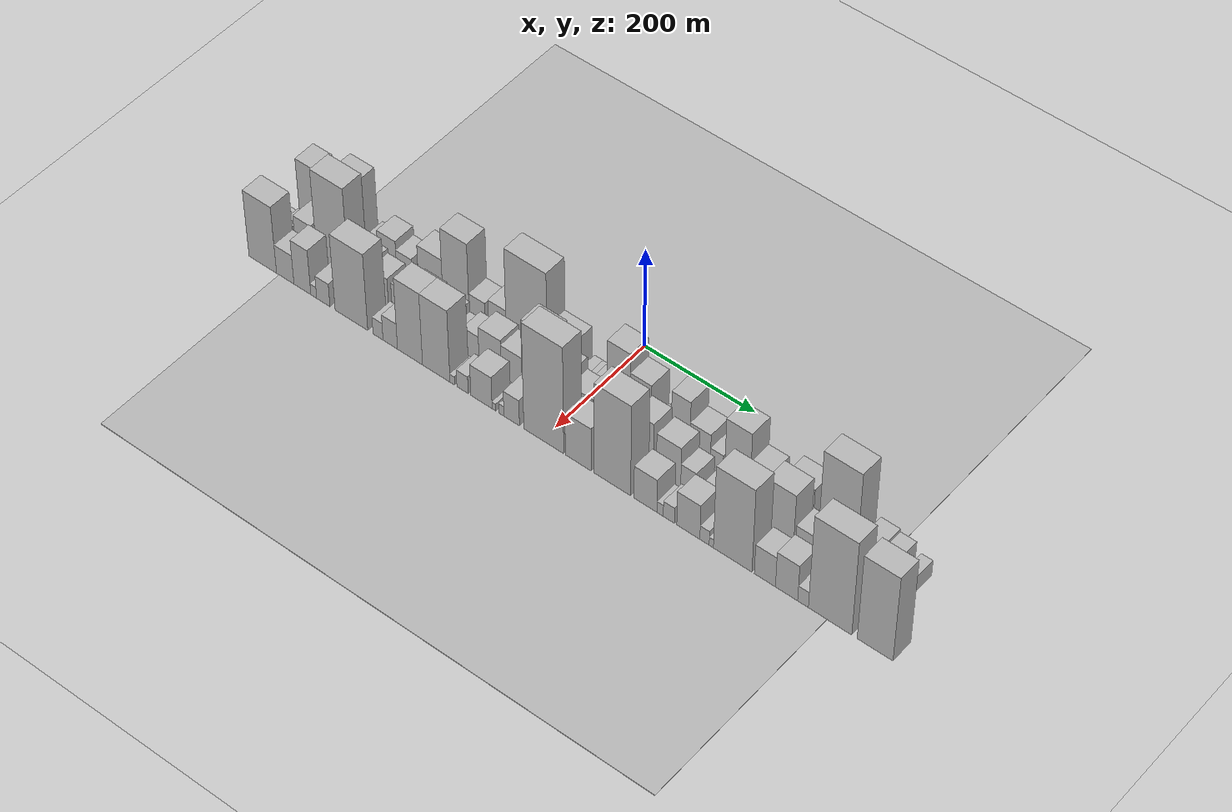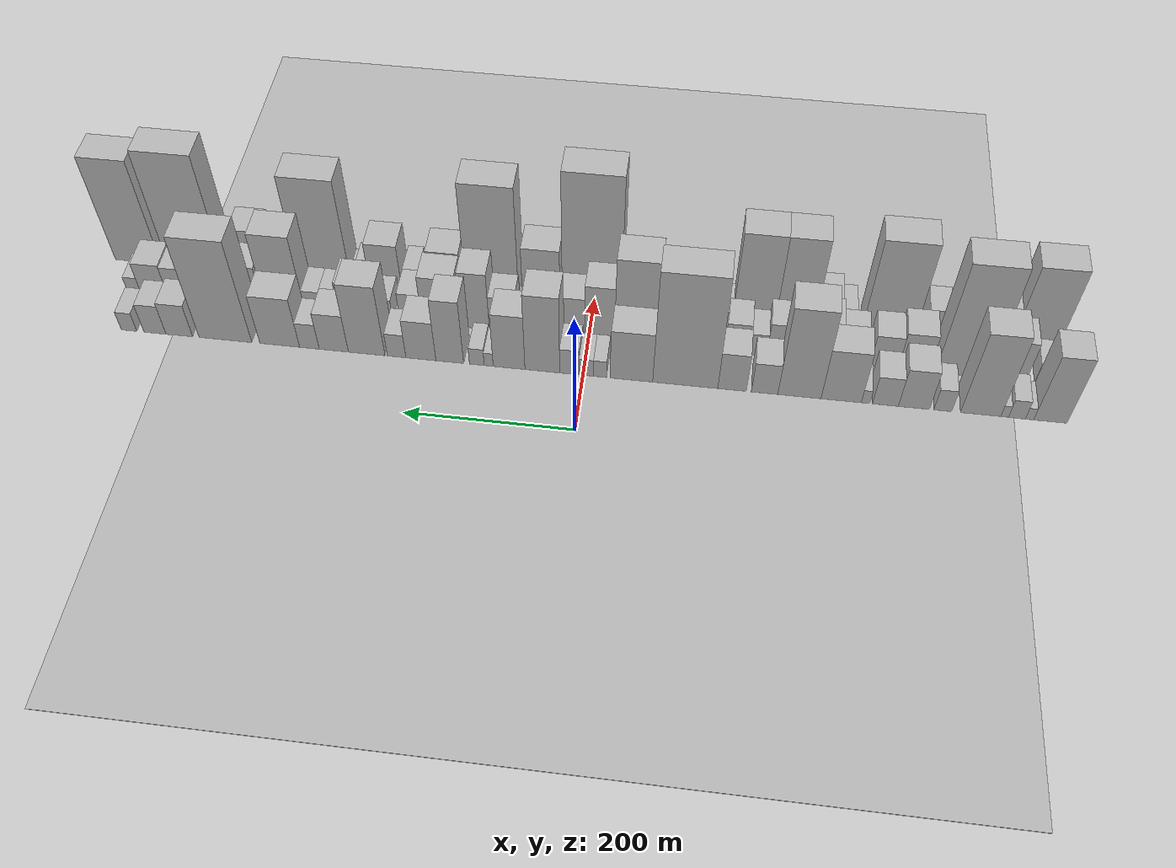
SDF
<?xml version="1.0" encoding="utf-8"?>

<sdf version="1.6">

   <world name="default">

      <gui fullscreen="0">

         <camera name="user_camera">

            <pose>-15 0 4.57585 0 0 0</pose>

            <view_controller>orbit</view_controller>

         </camera>

      </gui>

      <scene>

         <sky>

           <clouds>

             <speed>12</speed>

           </clouds>

         </sky>

         <ambient>0.4 0.4 0.4 1</ambient>

         <background>0.7 0.7 0.7 1</background>

         <shadows>1</shadows>

      </scene>

      <gravity>0 0 -9.8066</gravity>

      <magnetic_field>6e-06 2.3e-05 -4.2e-05</magnetic_field>

      <physics default="0" name="default_physics" type="ode">

         <ode>

            <solver>

               <type>quick</type>

               <iters>10</iters>

               <sor>1.0</sor>

               <use_dynamic_moi_rescaling>0</use_dynamic_moi_rescaling>

            </solver>

            <constraints>

               <cfm>0</cfm>

               <erp>0.2</erp>

               <contact_max_correcting_vel>100</contact_max_correcting_vel>

               <contact_surface_layer>0.001</contact_surface_layer>

            </constraints>

         </ode>

         <max_step_size>0.004</max_step_size>

         <real_time_factor>1</real_time_factor>

         <real_time_update_rate>250</real_time_update_rate>

      </physics>

      <light name="sun" type="directional">

         <cast_shadows>1</cast_shadows>

         <pose>0 0 10 0 0 0</pose>

         <diffuse>0.8 0.8 0.8 1</diffuse>

         <specular>0.2 0.2 0.2 1</specular>

         <attenuation>

            <range>1000</range>

            <constant>0.9</constant>

            <linear>0.01</linear>

            <quadratic>0.001</quadratic>

         </attenuation>

         <direction>-0.5 0.1 -0.9</direction>

      </light>

      <include>

         <name>ground_plane_1</name>

         <uri>model://HANNAS_ground_plane</uri>

         <pose>0 0 0  0 0 0</pose>

      </include>

      <include>

         <name>ground_plane_2</name>

         <uri>model://HANNAS_ground_plane</uri>

         <pose>100 0 0  0 0 0</pose>

      </include>

      <model name="building_1">

         <static>1</static>

         <pose frame="">100.0000 -541.2962 0 0.000000 0.000000 0.000000</pose>

         <link name="link">

            <pose frame="">0 0 58.50 0 0 0</pose>

            <collision name="collision">

               <geometry>

                  <box>

                     <size>40.0000 37.4076 117.0000</size>

                  </box>

               </geometry>

               <max_contacts>10</max_contacts>

               <surface>

                  <contact>

                     <ode/>

                  </contact>

                  <bounce/>

                  <friction>

                     <torsional>

                        <ode/>

                     </torsional>

                     <ode/>

                  </friction>

               </surface>

            </collision>

            <visual name="visual">

               <cast_shadows>0</cast_shadows>

               <geometry>

                  <box>

                     <size>40.0000 37.4076 117.0000</size>

                  </box>

               </geometry>

               <material>

                  <script>

                     <uri>model://HANNAS_wall/materials/scripts</uri>

                     <uri>model://HANNAS_wall/materials/textures</uri>

                     <name>vrc/HANNAS_wall</name>

                  </script>

               </material>

            </visual>

            <self_collide>0</self_collide>

            <enable_wind>0</enable_wind>

            <kinematic>0</kinematic>

         </link>

      </model>

      <model name="building_2">

         <static>1</static>

         <pose frame="">100.0000 -517.8946 0 0.000000 0.000000 0.000000</pose>

         <link name="link">

            <pose frame="">0 0 10.50 0 0 0</pose>

            <collision name="collision">

               <geometry>

                  <box>

                     <size>40.0000 9.3956 21.0000</size>

                  </box>

               </geometry>

               <max_contacts>10</max_contacts>

               <surface>

                  <contact>

                     <ode/>

                  </contact>

                  <bounce/>

                  <friction>

                     <torsional>

                        <ode/>

                     </torsional>

                     <ode/>

                  </friction>

               </surface>

            </collision>

            <visual name="visual">

               <cast_shadows>0</cast_shadows>

               <geometry>

                  <box>

                     <size>40.0000 9.3956 21.0000</size>

                  </box>

               </geometry>

               <material>

                  <script>

                     <uri>model://HANNAS_wall/materials/scripts</uri>

                     <uri>model://HANNAS_wall/materials/textures</uri>

                     <name>vrc/HANNAS_wall</name>

                  </script>

               </material>

            </visual>

            <self_collide>0</self_collide>

            <enable_wind>0</enable_wind>

            <kinematic>0</kinematic>

         </link>

      </model>

      <model name="building_3">

         <static>1</static>

         <pose frame="">100.0000 -503.5734 0 0.000000 0.000000 0.000000</pose>

         <link name="link">

            <pose frame="">0 0 16.50 0 0 0</pose>

            <collision name="collision">

               <geometry>

                  <box>

                     <size>40.0000 19.2466 33.0000</size>

                  </box>

               </geometry>

               <max_contacts>10</max_contacts>

               <surface>

                  <contact>

                     <ode/>

                  </contact>

                  <bounce/>

                  <friction>

                     <torsional>

                        <ode/>

                     </torsional>

                     <ode/>

                  </friction>

               </surface>

            </collision>

            <visual name="visual">

               <cast_shadows>0</cast_shadows>

               <geometry>

                  <box>

                     <size>40.0000 19.2466 33.0000</size>

                  </box>

               </geometry>

               <material>

                  <script>

                     <uri>model://HANNAS_wall/materials/scripts</uri>

                     <uri>model://HANNAS_wall/materials/textures</uri>

                     <name>vrc/HANNAS_wall</name>

                  </script>

               </material>

            </visual>

            <self_collide>0</self_collide>

            <enable_wind>0</enable_wind>

            <kinematic>0</kinematic>

         </link>

      </model>

      <model name="building_4">

         <static>1</static>

         <pose frame="">100.0000 -489.6087 0 0.000000 0.000000 0.000000</pose>

         <link name="link">

            <pose frame="">0 0 10.50 0 0 0</pose>

            <collision name="collision">

               <geometry>

                  <box>

                     <size>40.0000 8.6828 21.0000</size>

                  </box>

               </geometry>

               <max_contacts>10</max_contacts>

               <surface>

                  <contact>

                     <ode/>

                  </contact>

                  <bounce/>

                  <friction>

                     <torsional>

                        <ode/>

                     </torsional>

                     <ode/>

                  </friction>

               </surface>

            </collision>

            <visual name="visual">

               <cast_shadows>0</cast_shadows>

               <geometry>

                  <box>

                     <size>40.0000 8.6828 21.0000</size>

                  </box>

               </geometry>

               <material>

                  <script>

                     <uri>model://HANNAS_wall/materials/scripts</uri>

                     <uri>model://HANNAS_wall/materials/textures</uri>

                     <name>vrc/HANNAS_wall</name>

                  </script>

               </material>

            </visual>

            <self_collide>0</self_collide>

            <enable_wind>0</enable_wind>

            <kinematic>0</kinematic>

         </link>

      </model>

      <model name="building_5">

         <static>1</static>

         <pose frame="">100.0000 -462.3022 0 0.000000 0.000000 0.000000</pose>

         <link name="link">

            <pose frame="">0 0 72.00 0 0 0</pose>

            <collision name="collision">

               <geometry>

                  <box>

                     <size>40.0000 45.9303 144.0000</size>

                  </box>

               </geometry>

               <max_contacts>10</max_contacts>

               <surface>

                  <contact>

                     <ode/>

                  </contact>

                  <bounce/>

                  <friction>

                     <torsional>

                        <ode/>

                     </torsional>

                     <ode/>

                  </friction>

               </surface>

            </collision>

            <visual name="visual">

               <cast_shadows>0</cast_shadows>

               <geometry>

                  <box>

                     <size>40.0000 45.9303 144.0000</size>

                  </box>

               </geometry>

               <material>

                  <script>

                     <uri>model://HANNAS_wall/materials/scripts</uri>

                     <uri>model://HANNAS_wall/materials/textures</uri>

                     <name>vrc/HANNAS_wall</name>

                  </script>

               </material>

            </visual>

            <self_collide>0</self_collide>

            <enable_wind>0</enable_wind>

            <kinematic>0</kinematic>

         </link>

      </model>

      <model name="building_6">

         <static>1</static>

         <pose frame="">100.0000 -419.1466 0 0.000000 0.000000 0.000000</pose>

         <link name="link">

            <pose frame="">0 0 19.50 0 0 0</pose>

            <collision name="collision">

               <geometry>

                  <box>

                     <size>40.0000 20.3808 39.0000</size>

                  </box>

               </geometry>

               <max_contacts>10</max_contacts>

               <surface>

                  <contact>

                     <ode/>

                  </contact>

                  <bounce/>

                  <friction>

                     <torsional>

                        <ode/>

                     </torsional>

                     <ode/>

                  </friction>

               </surface>

            </collision>

            <visual name="visual">

               <cast_shadows>0</cast_shadows>

               <geometry>

                  <box>

                     <size>40.0000 20.3808 39.0000</size>

                  </box>

               </geometry>

               <material>

                  <script>

                     <uri>model://HANNAS_wall/materials/scripts</uri>

                     <uri>model://HANNAS_wall/materials/textures</uri>

                     <name>vrc/HANNAS_wall</name>

                  </script>

               </material>

            </visual>

            <self_collide>0</self_collide>

            <enable_wind>0</enable_wind>

            <kinematic>0</kinematic>

         </link>

      </model>

      <model name="building_7">

         <static>1</static>

         <pose frame="">100.0000 -386.0449 0 0.000000 0.000000 0.000000</pose>

         <link name="link">

            <pose frame="">0 0 34.50 0 0 0</pose>

            <collision name="collision">

               <geometry>

                  <box>

                     <size>40.0000 35.8226 69.0000</size>

                  </box>

               </geometry>

               <max_contacts>10</max_contacts>

               <surface>

                  <contact>

                     <ode/>

                  </contact>

                  <bounce/>

                  <friction>

                     <torsional>

                        <ode/>

                     </torsional>

                     <ode/>

                  </friction>

               </surface>

            </collision>

            <visual name="visual">

               <cast_shadows>0</cast_shadows>

               <geometry>

                  <box>

                     <size>40.0000 35.8226 69.0000</size>

                  </box>

               </geometry>

               <material>

                  <script>

                     <uri>model://HANNAS_wall/materials/scripts</uri>

                     <uri>model://HANNAS_wall/materials/textures</uri>

                     <name>vrc/HANNAS_wall</name>

                  </script>

               </material>

            </visual>

            <self_collide>0</self_collide>

            <enable_wind>0</enable_wind>

            <kinematic>0</kinematic>

         </link>

      </model>

      <model name="building_8">

         <static>1</static>

         <pose frame="">100.0000 -353.2586 0 0.000000 0.000000 0.000000</pose>

         <link name="link">

            <pose frame="">0 0 25.50 0 0 0</pose>

            <collision name="collision">

               <geometry>

                  <box>

                     <size>40.0000 29.7500 51.0000</size>

                  </box>

               </geometry>

               <max_contacts>10</max_contacts>

               <surface>

                  <contact>

                     <ode/>

                  </contact>

                  <bounce/>

                  <friction>

                     <torsional>

                        <ode/>

                     </torsional>

                     <ode/>

                  </friction>

               </surface>

            </collision>

            <visual name="visual">

               <cast_shadows>0</cast_shadows>

               <geometry>

                  <box>

                     <size>40.0000 29.7500 51.0000</size>

                  </box>

               </geometry>

               <material>

                  <script>

                     <uri>model://HANNAS_wall/materials/scripts</uri>

                     <uri>model://HANNAS_wall/materials/textures</uri>

                     <name>vrc/HANNAS_wall</name>

                  </script>

               </material>

            </visual>

            <self_collide>0</self_collide>

            <enable_wind>0</enable_wind>

            <kinematic>0</kinematic>

         </link>

      </model>

      <model name="building_9">

         <static>1</static>

         <pose frame="">100.0000 -330.4575 0 0.000000 0.000000 0.000000</pose>

         <link name="link">

            <pose frame="">0 0 12.00 0 0 0</pose>

            <collision name="collision">

               <geometry>

                  <box>

                     <size>40.0000 9.8521 24.0000</size>

                  </box>

               </geometry>

               <max_contacts>10</max_contacts>

               <surface>

                  <contact>

                     <ode/>

                  </contact>

                  <bounce/>

                  <friction>

                     <torsional>

                        <ode/>

                     </torsional>

                     <ode/>

                  </friction>

               </surface>

            </collision>

            <visual name="visual">

               <cast_shadows>0</cast_shadows>

               <geometry>

                  <box>

                     <size>40.0000 9.8521 24.0000</size>

                  </box>

               </geometry>

               <material>

                  <script>

                     <uri>model://HANNAS_wall/materials/scripts</uri>

                     <uri>model://HANNAS_wall/materials/textures</uri>

                     <name>vrc/HANNAS_wall</name>

                  </script>

               </material>

            </visual>

            <self_collide>0</self_collide>

            <enable_wind>0</enable_wind>

            <kinematic>0</kinematic>

         </link>

      </model>

      <model name="building_10">

         <static>1</static>

         <pose frame="">100.0000 -302.2651 0 0.000000 0.000000 0.000000</pose>

         <link name="link">

            <pose frame="">0 0 45.00 0 0 0</pose>

            <collision name="collision">

               <geometry>

                  <box>

                     <size>40.0000 46.5325 90.0000</size>

                  </box>

               </geometry>

               <max_contacts>10</max_contacts>

               <surface>

                  <contact>

                     <ode/>

                  </contact>

                  <bounce/>

                  <friction>

                     <torsional>

                        <ode/>

                     </torsional>

                     <ode/>

                  </friction>

               </surface>

            </collision>

            <visual name="visual">

               <cast_shadows>0</cast_shadows>

               <geometry>

                  <box>

                     <size>40.0000 46.5325 90.0000</size>

                  </box>

               </geometry>

               <material>

                  <script>

                     <uri>model://HANNAS_wall/materials/scripts</uri>

                     <uri>model://HANNAS_wall/materials/textures</uri>

                     <name>vrc/HANNAS_wall</name>

                  </script>

               </material>

            </visual>

            <self_collide>0</self_collide>

            <enable_wind>0</enable_wind>

            <kinematic>0</kinematic>

         </link>

      </model>

      <model name="building_11">

         <static>1</static>

         <pose frame="">100.0000 -253.8668 0 0.000000 0.000000 0.000000</pose>

         <link name="link">

            <pose frame="">0 0 78.00 0 0 0</pose>

            <collision name="collision">

               <geometry>

                  <box>

                     <size>40.0000 50.2642 156.0000</size>

                  </box>

               </geometry>

               <max_contacts>10</max_contacts>

               <surface>

                  <contact>

                     <ode/>

                  </contact>

                  <bounce/>

                  <friction>

                     <torsional>

                        <ode/>

                     </torsional>

                     <ode/>

                  </friction>

               </surface>

            </collision>

            <visual name="visual">

               <cast_shadows>0</cast_shadows>

               <geometry>

                  <box>

                     <size>40.0000 50.2642 156.0000</size>

                  </box>

               </geometry>

               <material>

                  <script>

                     <uri>model://HANNAS_wall/materials/scripts</uri>

                     <uri>model://HANNAS_wall/materials/textures</uri>

                     <name>vrc/HANNAS_wall</name>

                  </script>

               </material>

            </visual>

            <self_collide>0</self_collide>

            <enable_wind>0</enable_wind>

            <kinematic>0</kinematic>

         </link>

      </model>

      <model name="building_12">

         <static>1</static>

         <pose frame="">100.0000 -213.3457 0 0.000000 0.000000 0.000000</pose>

         <link name="link">

            <pose frame="">0 0 27.00 0 0 0</pose>

            <collision name="collision">

               <geometry>

                  <box>

                     <size>40.0000 30.7780 54.0000</size>

                  </box>

               </geometry>

               <max_contacts>10</max_contacts>

               <surface>

                  <contact>

                     <ode/>

                  </contact>

                  <bounce/>

                  <friction>

                     <torsional>

                        <ode/>

                     </torsional>

                     <ode/>

                  </friction>

               </surface>

            </collision>

            <visual name="visual">

               <cast_shadows>0</cast_shadows>

               <geometry>

                  <box>

                     <size>40.0000 30.7780 54.0000</size>

                  </box>

               </geometry>

               <material>

                  <script>

                     <uri>model://HANNAS_wall/materials/scripts</uri>

                     <uri>model://HANNAS_wall/materials/textures</uri>

                     <name>vrc/HANNAS_wall</name>

                  </script>

               </material>

            </visual>

            <self_collide>0</self_collide>

            <enable_wind>0</enable_wind>

            <kinematic>0</kinematic>

         </link>

      </model>

      <model name="building_13">

         <static>1</static>

         <pose frame="">100.0000 -175.3187 0 0.000000 0.000000 0.000000</pose>

         <link name="link">

            <pose frame="">0 0 33.00 0 0 0</pose>

            <collision name="collision">

               <geometry>

                  <box>

                     <size>40.0000 33.2759 66.0000</size>

                  </box>

               </geometry>

               <max_contacts>10</max_contacts>

               <surface>

                  <contact>

                     <ode/>

                  </contact>

                  <bounce/>

                  <friction>

                     <torsional>

                        <ode/>

                     </torsional>

                     <ode/>

                  </friction>

               </surface>

            </collision>

            <visual name="visual">

               <cast_shadows>0</cast_shadows>

               <geometry>

                  <box>

                     <size>40.0000 33.2759 66.0000</size>

                  </box>

               </geometry>

               <material>

                  <script>

                     <uri>model://HANNAS_wall/materials/scripts</uri>

                     <uri>model://HANNAS_wall/materials/textures</uri>

                     <name>vrc/HANNAS_wall</name>

                  </script>

               </material>

            </visual>

            <self_collide>0</self_collide>

            <enable_wind>0</enable_wind>

            <kinematic>0</kinematic>

         </link>

      </model>

      <model name="building_14">

         <static>1</static>

         <pose frame="">100.0000 -120.3680 0 0.000000 0.000000 0.000000</pose>

         <link name="link">

            <pose frame="">0 0 97.50 0 0 0</pose>

            <collision name="collision">

               <geometry>

                  <box>

                     <size>40.0000 76.6255 195.0000</size>

                  </box>

               </geometry>

               <max_contacts>10</max_contacts>

               <surface>

                  <contact>

                     <ode/>

                  </contact>

                  <bounce/>

                  <friction>

                     <torsional>

                        <ode/>

                     </torsional>

                     <ode/>

                  </friction>

               </surface>

            </collision>

            <visual name="visual">

               <cast_shadows>0</cast_shadows>

               <geometry>

                  <box>

                     <size>40.0000 76.6255 195.0000</size>

                  </box>

               </geometry>

               <material>

                  <script>

                     <uri>model://HANNAS_wall/materials/scripts</uri>

                     <uri>model://HANNAS_wall/materials/textures</uri>

                     <name>vrc/HANNAS_wall</name>

                  </script>

               </material>

            </visual>

            <self_collide>0</self_collide>

            <enable_wind>0</enable_wind>

            <kinematic>0</kinematic>

         </link>

      </model>

      <model name="building_15">

         <static>1</static>

         <pose frame="">100.0000 -56.7692 0 0.000000 0.000000 0.000000</pose>

         <link name="link">

            <pose frame="">0 0 43.50 0 0 0</pose>

            <collision name="collision">

               <geometry>

                  <box>

                     <size>40.0000 50.5721 87.0000</size>

                  </box>

               </geometry>

               <max_contacts>10</max_contacts>

               <surface>

                  <contact>

                     <ode/>

                  </contact>

                  <bounce/>

                  <friction>

                     <torsional>

                        <ode/>

                     </torsional>

                     <ode/>

                  </friction>

               </surface>

            </collision>

            <visual name="visual">

               <cast_shadows>0</cast_shadows>

               <geometry>

                  <box>

                     <size>40.0000 50.5721 87.0000</size>

                  </box>

               </geometry>

               <material>

                  <script>

                     <uri>model://HANNAS_wall/materials/scripts</uri>

                     <uri>model://HANNAS_wall/materials/textures</uri>

                     <name>vrc/HANNAS_wall</name>

                  </script>

               </material>

            </visual>

            <self_collide>0</self_collide>

            <enable_wind>0</enable_wind>

            <kinematic>0</kinematic>

         </link>

      </model>

      <model name="building_16">

         <static>1</static>

         <pose frame="">100.0000 -19.5867 0 0.000000 0.000000 0.000000</pose>

         <link name="link">

            <pose frame="">0 0 15.00 0 0 0</pose>

            <collision name="collision">

               <geometry>

                  <box>

                     <size>40.0000 15.7928 30.0000</size>

                  </box>

               </geometry>

               <max_contacts>10</max_contacts>

               <surface>

                  <contact>

                     <ode/>

                  </contact>

                  <bounce/>

                  <friction>

                     <torsional>

                        <ode/>

                     </torsional>

                     <ode/>

                  </friction>

               </surface>

            </collision>

            <visual name="visual">

               <cast_shadows>0</cast_shadows>

               <geometry>

                  <box>

                     <size>40.0000 15.7928 30.0000</size>

                  </box>

               </geometry>

               <material>

                  <script>

                     <uri>model://HANNAS_wall/materials/scripts</uri>

                     <uri>model://HANNAS_wall/materials/textures</uri>

                     <name>vrc/HANNAS_wall</name>

                  </script>

               </material>

            </visual>

            <self_collide>0</self_collide>

            <enable_wind>0</enable_wind>

            <kinematic>0</kinematic>

         </link>

      </model>

      <model name="building_17">

         <static>1</static>

         <pose frame="">100.0000 -3.1925 0 0.000000 0.000000 0.000000</pose>

         <link name="link">

            <pose frame="">0 0 15.00 0 0 0</pose>

            <collision name="collision">

               <geometry>

                  <box>

                     <size>40.0000 16.9956 30.0000</size>

                  </box>

               </geometry>

               <max_contacts>10</max_contacts>

               <surface>

                  <contact>

                     <ode/>

                  </contact>

                  <bounce/>

                  <friction>

                     <torsional>

                        <ode/>

                     </torsional>

                     <ode/>

                  </friction>

               </surface>

            </collision>

            <visual name="visual">

               <cast_shadows>0</cast_shadows>

               <geometry>

                  <box>

                     <size>40.0000 16.9956 30.0000</size>

                  </box>

               </geometry>

               <material>

                  <script>

                     <uri>model://HANNAS_wall/materials/scripts</uri>

                     <uri>model://HANNAS_wall/materials/textures</uri>

                     <name>vrc/HANNAS_wall</name>

                  </script>

               </material>

            </visual>

            <self_collide>0</self_collide>

            <enable_wind>0</enable_wind>

            <kinematic>0</kinematic>

         </link>

      </model>

      <model name="building_18">

         <static>1</static>

         <pose frame="">100.0000 16.7724 0 0.000000 0.000000 0.000000</pose>

         <link name="link">

            <pose frame="">0 0 22.50 0 0 0</pose>

            <collision name="collision">

               <geometry>

                  <box>

                     <size>40.0000 22.9341 45.0000</size>

                  </box>

               </geometry>

               <max_contacts>10</max_contacts>

               <surface>

                  <contact>

                     <ode/>

                  </contact>

                  <bounce/>

                  <friction>

                     <torsional>

                        <ode/>

                     </torsional>

                     <ode/>

                  </friction>

               </surface>

            </collision>

            <visual name="visual">

               <cast_shadows>0</cast_shadows>

               <geometry>

                  <box>

                     <size>40.0000 22.9341 45.0000</size>

                  </box>

               </geometry>

               <material>

                  <script>

                     <uri>model://HANNAS_wall/materials/scripts</uri>

                     <uri>model://HANNAS_wall/materials/textures</uri>

                     <name>vrc/HANNAS_wall</name>

                  </script>

               </material>

            </visual>

            <self_collide>0</self_collide>

            <enable_wind>0</enable_wind>

            <kinematic>0</kinematic>

         </link>

      </model>

      <model name="building_19">

         <static>1</static>

         <pose frame="">100.0000 48.9678 0 0.000000 0.000000 0.000000</pose>

         <link name="link">

            <pose frame="">0 0 67.50 0 0 0</pose>

            <collision name="collision">

               <geometry>

                  <box>

                     <size>40.0000 41.4567 135.0000</size>

                  </box>

               </geometry>

               <max_contacts>10</max_contacts>

               <surface>

                  <contact>

                     <ode/>

                  </contact>

                  <bounce/>

                  <friction>

                     <torsional>

                        <ode/>

                     </torsional>

                     <ode/>

                  </friction>

               </surface>

            </collision>

            <visual name="visual">

               <cast_shadows>0</cast_shadows>

               <geometry>

                  <box>

                     <size>40.0000 41.4567 135.0000</size>

                  </box>

               </geometry>

               <material>

                  <script>

                     <uri>model://HANNAS_wall/materials/scripts</uri>

                     <uri>model://HANNAS_wall/materials/textures</uri>

                     <name>vrc/HANNAS_wall</name>

                  </script>

               </material>

            </visual>

            <self_collide>0</self_collide>

            <enable_wind>0</enable_wind>

            <kinematic>0</kinematic>

         </link>

      </model>

      <model name="building_20">

         <static>1</static>

         <pose frame="">100.0000 88.7517 0 0.000000 0.000000 0.000000</pose>

         <link name="link">

            <pose frame="">0 0 48.00 0 0 0</pose>

            <collision name="collision">

               <geometry>

                  <box>

                     <size>40.0000 38.1110 96.0000</size>

                  </box>

               </geometry>

               <max_contacts>10</max_contacts>

               <surface>

                  <contact>

                     <ode/>

                  </contact>

                  <bounce/>

                  <friction>

                     <torsional>

                        <ode/>

                     </torsional>

                     <ode/>

                  </friction>

               </surface>

            </collision>

            <visual name="visual">

               <cast_shadows>0</cast_shadows>

               <geometry>

                  <box>

                     <size>40.0000 38.1110 96.0000</size>

                  </box>

               </geometry>

               <material>

                  <script>

                     <uri>model://HANNAS_wall/materials/scripts</uri>

                     <uri>model://HANNAS_wall/materials/textures</uri>

                     <name>vrc/HANNAS_wall</name>

                  </script>

               </material>

            </visual>

            <self_collide>0</self_collide>

            <enable_wind>0</enable_wind>

            <kinematic>0</kinematic>

         </link>

      </model>

      <model name="building_21">

         <static>1</static>

         <pose frame="">100.0000 113.2145 0 0.000000 0.000000 0.000000</pose>

         <link name="link">

            <pose frame="">0 0 12.00 0 0 0</pose>

            <collision name="collision">

               <geometry>

                  <box>

                     <size>40.0000 10.8146 24.0000</size>

                  </box>

               </geometry>

               <max_contacts>10</max_contacts>

               <surface>

                  <contact>

                     <ode/>

                  </contact>

                  <bounce/>

                  <friction>

                     <torsional>

                        <ode/>

                     </torsional>

                     <ode/>

                  </friction>

               </surface>

            </collision>

            <visual name="visual">

               <cast_shadows>0</cast_shadows>

               <geometry>

                  <box>

                     <size>40.0000 10.8146 24.0000</size>

                  </box>

               </geometry>

               <material>

                  <script>

                     <uri>model://HANNAS_wall/materials/scripts</uri>

                     <uri>model://HANNAS_wall/materials/textures</uri>

                     <name>vrc/HANNAS_wall</name>

                  </script>

               </material>

            </visual>

            <self_collide>0</self_collide>

            <enable_wind>0</enable_wind>

            <kinematic>0</kinematic>

         </link>

      </model>

      <model name="building_22">

         <static>1</static>

         <pose frame="">100.0000 127.5079 0 0.000000 0.000000 0.000000</pose>

         <link name="link">

            <pose frame="">0 0 15.00 0 0 0</pose>

            <collision name="collision">

               <geometry>

                  <box>

                     <size>40.0000 17.7722 30.0000</size>

                  </box>

               </geometry>

               <max_contacts>10</max_contacts>

               <surface>

                  <contact>

                     <ode/>

                  </contact>

                  <bounce/>

                  <friction>

                     <torsional>

                        <ode/>

                     </torsional>

                     <ode/>

                  </friction>

               </surface>

            </collision>

            <visual name="visual">

               <cast_shadows>0</cast_shadows>

               <geometry>

                  <box>

                     <size>40.0000 17.7722 30.0000</size>

                  </box>

               </geometry>

               <material>

                  <script>

                     <uri>model://HANNAS_wall/materials/scripts</uri>

                     <uri>model://HANNAS_wall/materials/textures</uri>

                     <name>vrc/HANNAS_wall</name>

                  </script>

               </material>

            </visual>

            <self_collide>0</self_collide>

            <enable_wind>0</enable_wind>

            <kinematic>0</kinematic>

         </link>

      </model>

      <model name="building_23">

         <static>1</static>

         <pose frame="">100.0000 160.1324 0 0.000000 0.000000 0.000000</pose>

         <link name="link">

            <pose frame="">0 0 55.50 0 0 0</pose>

            <collision name="collision">

               <geometry>

                  <box>

                     <size>40.0000 33.4768 111.0000</size>

                  </box>

               </geometry>

               <max_contacts>10</max_contacts>

               <surface>

                  <contact>

                     <ode/>

                  </contact>

                  <bounce/>

                  <friction>

                     <torsional>

                        <ode/>

                     </torsional>

                     <ode/>

                  </friction>

               </surface>

            </collision>

            <visual name="visual">

               <cast_shadows>0</cast_shadows>

               <geometry>

                  <box>

                     <size>40.0000 33.4768 111.0000</size>

                  </box>

               </geometry>

               <material>

                  <script>

                     <uri>model://HANNAS_wall/materials/scripts</uri>

                     <uri>model://HANNAS_wall/materials/textures</uri>

                     <name>vrc/HANNAS_wall</name>

                  </script>

               </material>

            </visual>

            <self_collide>0</self_collide>

            <enable_wind>0</enable_wind>

            <kinematic>0</kinematic>

         </link>

      </model>

      <model name="building_24">

         <static>1</static>

         <pose frame="">100.0000 195.0404 0 0.000000 0.000000 0.000000</pose>

         <link name="link">

            <pose frame="">0 0 34.50 0 0 0</pose>

            <collision name="collision">

               <geometry>

                  <box>

                     <size>40.0000 36.3392 69.0000</size>

                  </box>

               </geometry>

               <max_contacts>10</max_contacts>

               <surface>

                  <contact>

                     <ode/>

                  </contact>

                  <bounce/>

                  <friction>

                     <torsional>

                        <ode/>

                     </torsional>

                     <ode/>

                  </friction>

               </surface>

            </collision>

            <visual name="visual">

               <cast_shadows>0</cast_shadows>

               <geometry>

                  <box>

                     <size>40.0000 36.3392 69.0000</size>

                  </box>

               </geometry>

               <material>

                  <script>

                     <uri>model://HANNAS_wall/materials/scripts</uri>

                     <uri>model://HANNAS_wall/materials/textures</uri>

                     <name>vrc/HANNAS_wall</name>

                  </script>

               </material>

            </visual>

            <self_collide>0</self_collide>

            <enable_wind>0</enable_wind>

            <kinematic>0</kinematic>

         </link>

      </model>

      <model name="building_25">

         <static>1</static>

         <pose frame="">100.0000 224.4524 0 0.000000 0.000000 0.000000</pose>

         <link name="link">

            <pose frame="">0 0 21.00 0 0 0</pose>

            <collision name="collision">

               <geometry>

                  <box>

                     <size>40.0000 22.4849 42.0000</size>

                  </box>

               </geometry>

               <max_contacts>10</max_contacts>

               <surface>

                  <contact>

                     <ode/>

                  </contact>

                  <bounce/>

                  <friction>

                     <torsional>

                        <ode/>

                     </torsional>

                     <ode/>

                  </friction>

               </surface>

            </collision>

            <visual name="visual">

               <cast_shadows>0</cast_shadows>

               <geometry>

                  <box>

                     <size>40.0000 22.4849 42.0000</size>

                  </box>

               </geometry>

               <material>

                  <script>

                     <uri>model://HANNAS_wall/materials/scripts</uri>

                     <uri>model://HANNAS_wall/materials/textures</uri>

                     <name>vrc/HANNAS_wall</name>

                  </script>

               </material>

            </visual>

            <self_collide>0</self_collide>

            <enable_wind>0</enable_wind>

            <kinematic>0</kinematic>

         </link>

      </model>

      <model name="building_26">

         <static>1</static>

         <pose frame="">100.0000 260.9989 0 0.000000 0.000000 0.000000</pose>

         <link name="link">

            <pose frame="">0 0 61.50 0 0 0</pose>

            <collision name="collision">

               <geometry>

                  <box>

                     <size>40.0000 44.6081 123.0000</size>

                  </box>

               </geometry>

               <max_contacts>10</max_contacts>

               <surface>

                  <contact>

                     <ode/>

                  </contact>

                  <bounce/>

                  <friction>

                     <torsional>

                        <ode/>

                     </torsional>

                     <ode/>

                  </friction>

               </surface>

            </collision>

            <visual name="visual">

               <cast_shadows>0</cast_shadows>

               <geometry>

                  <box>

                     <size>40.0000 44.6081 123.0000</size>

                  </box>

               </geometry>

               <material>

                  <script>

                     <uri>model://HANNAS_wall/materials/scripts</uri>

                     <uri>model://HANNAS_wall/materials/textures</uri>

                     <name>vrc/HANNAS_wall</name>

                  </script>

               </material>

            </visual>

            <self_collide>0</self_collide>

            <enable_wind>0</enable_wind>

            <kinematic>0</kinematic>

         </link>

      </model>

      <model name="building_27">

         <static>1</static>

         <pose frame="">100.0000 301.1546 0 0.000000 0.000000 0.000000</pose>

         <link name="link">

            <pose frame="">0 0 33.00 0 0 0</pose>

            <collision name="collision">

               <geometry>

                  <box>

                     <size>40.0000 35.7034 66.0000</size>

                  </box>

               </geometry>

               <max_contacts>10</max_contacts>

               <surface>

                  <contact>

                     <ode/>

                  </contact>

                  <bounce/>

                  <friction>

                     <torsional>

                        <ode/>

                     </torsional>

                     <ode/>

                  </friction>

               </surface>

            </collision>

            <visual name="visual">

               <cast_shadows>0</cast_shadows>

               <geometry>

                  <box>

                     <size>40.0000 35.7034 66.0000</size>

                  </box>

               </geometry>

               <material>

                  <script>

                     <uri>model://HANNAS_wall/materials/scripts</uri>

                     <uri>model://HANNAS_wall/materials/textures</uri>

                     <name>vrc/HANNAS_wall</name>

                  </script>

               </material>

            </visual>

            <self_collide>0</self_collide>

            <enable_wind>0</enable_wind>

            <kinematic>0</kinematic>

         </link>

      </model>

      <model name="building_28">

         <static>1</static>

         <pose frame="">100.0000 331.0335 0 0.000000 0.000000 0.000000</pose>

         <link name="link">

            <pose frame="">0 0 22.50 0 0 0</pose>

            <collision name="collision">

               <geometry>

                  <box>

                     <size>40.0000 24.0544 45.0000</size>

                  </box>

               </geometry>

               <max_contacts>10</max_contacts>

               <surface>

                  <contact>

                     <ode/>

                  </contact>

                  <bounce/>

                  <friction>

                     <torsional>

                        <ode/>

                     </torsional>

                     <ode/>

                  </friction>

               </surface>

            </collision>

            <visual name="visual">

               <cast_shadows>0</cast_shadows>

               <geometry>

                  <box>

                     <size>40.0000 24.0544 45.0000</size>

                  </box>

               </geometry>

               <material>

                  <script>

                     <uri>model://HANNAS_wall/materials/scripts</uri>

                     <uri>model://HANNAS_wall/materials/textures</uri>

                     <name>vrc/HANNAS_wall</name>

                  </script>

               </material>

            </visual>

            <self_collide>0</self_collide>

            <enable_wind>0</enable_wind>

            <kinematic>0</kinematic>

         </link>

      </model>

      <model name="building_29">

         <static>1</static>

         <pose frame="">100.0000 367.5240 0 0.000000 0.000000 0.000000</pose>

         <link name="link">

            <pose frame="">0 0 43.50 0 0 0</pose>

            <collision name="collision">

               <geometry>

                  <box>

                     <size>40.0000 48.9265 87.0000</size>

                  </box>

               </geometry>

               <max_contacts>10</max_contacts>

               <surface>

                  <contact>

                     <ode/>

                  </contact>

                  <bounce/>

                  <friction>

                     <torsional>

                        <ode/>

                     </torsional>

                     <ode/>

                  </friction>

               </surface>

            </collision>

            <visual name="visual">

               <cast_shadows>0</cast_shadows>

               <geometry>

                  <box>

                     <size>40.0000 48.9265 87.0000</size>

                  </box>

               </geometry>

               <material>

                  <script>

                     <uri>model://HANNAS_wall/materials/scripts</uri>

                     <uri>model://HANNAS_wall/materials/textures</uri>

                     <name>vrc/HANNAS_wall</name>

                  </script>

               </material>

            </visual>

            <self_collide>0</self_collide>

            <enable_wind>0</enable_wind>

            <kinematic>0</kinematic>

         </link>

      </model>

      <model name="building_30">

         <static>1</static>

         <pose frame="">100.0000 434.6717 0 0.000000 0.000000 0.000000</pose>

         <link name="link">

            <pose frame="">0 0 88.50 0 0 0</pose>

            <collision name="collision">

               <geometry>

                  <box>

                     <size>40.0000 65.3691 177.0000</size>

                  </box>

               </geometry>

               <max_contacts>10</max_contacts>

               <surface>

                  <contact>

                     <ode/>

                  </contact>

                  <bounce/>

                  <friction>

                     <torsional>

                        <ode/>

                     </torsional>

                     <ode/>

                  </friction>

               </surface>

            </collision>

            <visual name="visual">

               <cast_shadows>0</cast_shadows>

               <geometry>

                  <box>

                     <size>40.0000 65.3691 177.0000</size>

                  </box>

               </geometry>

               <material>

                  <script>

                     <uri>model://HANNAS_wall/materials/scripts</uri>

                     <uri>model://HANNAS_wall/materials/textures</uri>

                     <name>vrc/HANNAS_wall</name>

                  </script>

               </material>

            </visual>

            <self_collide>0</self_collide>

            <enable_wind>0</enable_wind>

            <kinematic>0</kinematic>

         </link>

      </model>

      <model name="building_31">

         <static>1</static>

         <pose frame="">100.0000 491.9716 0 0.000000 0.000000 0.000000</pose>

         <link name="link">

            <pose frame="">0 0 28.50 0 0 0</pose>

            <collision name="collision">

               <geometry>

                  <box>

                     <size>40.0000 33.2307 57.0000</size>

                  </box>

               </geometry>

               <max_contacts>10</max_contacts>

               <surface>

                  <contact>

                     <ode/>

                  </contact>

                  <bounce/>

                  <friction>

                     <torsional>

                        <ode/>

                     </torsional>

                     <ode/>

                  </friction>

               </surface>

            </collision>

            <visual name="visual">

               <cast_shadows>0</cast_shadows>

               <geometry>

                  <box>

                     <size>40.0000 33.2307 57.0000</size>

                  </box>

               </geometry>

               <material>

                  <script>

                     <uri>model://HANNAS_wall/materials/scripts</uri>

                     <uri>model://HANNAS_wall/materials/textures</uri>

                     <name>vrc/HANNAS_wall</name>

                  </script>

               </material>

            </visual>

            <self_collide>0</self_collide>

            <enable_wind>0</enable_wind>

            <kinematic>0</kinematic>

         </link>

      </model>

      <model name="building_32">

         <static>1</static>

         <pose frame="">100.0000 522.3087 0 0.000000 0.000000 0.000000</pose>

         <link name="link">

            <pose frame="">0 0 25.50 0 0 0</pose>

            <collision name="collision">

               <geometry>

                  <box>

                     <size>40.0000 27.4435 51.0000</size>

                  </box>

               </geometry>

               <max_contacts>10</max_contacts>

               <surface>

                  <contact>

                     <ode/>

                  </contact>

                  <bounce/>

                  <friction>

                     <torsional>

                        <ode/>

                     </torsional>

                     <ode/>

                  </friction>

               </surface>

            </collision>

            <visual name="visual">

               <cast_shadows>0</cast_shadows>

               <geometry>

                  <box>

                     <size>40.0000 27.4435 51.0000</size>

                  </box>

               </geometry>

               <material>

                  <script>

                     <uri>model://HANNAS_wall/materials/scripts</uri>

                     <uri>model://HANNAS_wall/materials/textures</uri>

                     <name>vrc/HANNAS_wall</name>

                  </script>

               </material>

            </visual>

            <self_collide>0</self_collide>

            <enable_wind>0</enable_wind>

            <kinematic>0</kinematic>

         </link>

      </model>

      <model name="building_33">

         <static>1</static>

         <pose frame="">100.0000 554.6886 0 0.000000 0.000000 0.000000</pose>

         <link name="link">

            <pose frame="">0 0 16.50 0 0 0</pose>

            <collision name="collision">

               <geometry>

                  <box>

                     <size>40.0000 19.3164 33.0000</size>

                  </box>

               </geometry>

               <max_contacts>10</max_contacts>

               <surface>

                  <contact>

                     <ode/>

                  </contact>

                  <bounce/>

                  <friction>

                     <torsional>

                        <ode/>

                     </torsional>

                     <ode/>

                  </friction>

               </surface>

            </collision>

            <visual name="visual">

               <cast_shadows>0</cast_shadows>

               <geometry>

                  <box>

                     <size>40.0000 19.3164 33.0000</size>

                  </box>

               </geometry>

               <material>

                  <script>

                     <uri>model://HANNAS_wall/materials/scripts</uri>

                     <uri>model://HANNAS_wall/materials/textures</uri>

                     <name>vrc/HANNAS_wall</name>

                  </script>

               </material>

            </visual>

            <self_collide>0</self_collide>

            <enable_wind>0</enable_wind>

            <kinematic>0</kinematic>

         </link>

      </model>

      <model name="building_34">

         <static>1</static>

         <pose frame="">155.0000 -553.3637 0 0.000000 0.000000 0.000000</pose>

         <link name="link">

            <pose frame="">0 0 13.50 0 0 0</pose>

            <collision name="collision">

               <geometry>

                  <box>

                     <size>40.0000 13.2726 27.0000</size>

                  </box>

               </geometry>

               <max_contacts>10</max_contacts>

               <surface>

                  <contact>

                     <ode/>

                  </contact>

                  <bounce/>

                  <friction>

                     <torsional>

                        <ode/>

                     </torsional>

                     <ode/>

                  </friction>

               </surface>

            </collision>

            <visual name="visual">

               <cast_shadows>0</cast_shadows>

               <geometry>

                  <box>

                     <size>40.0000 13.2726 27.0000</size>

                  </box>

               </geometry>

               <material>

                  <script>

                     <uri>model://HANNAS_wall/materials/scripts</uri>

                     <uri>model://HANNAS_wall/materials/textures</uri>

                     <name>vrc/HANNAS_wall</name>

                  </script>

               </material>

            </visual>

            <self_collide>0</self_collide>

            <enable_wind>0</enable_wind>

            <kinematic>0</kinematic>

         </link>

      </model>

      <model name="building_35">

         <static>1</static>

         <pose frame="">155.0000 -537.4298 0 0.000000 0.000000 0.000000</pose>

         <link name="link">

            <pose frame="">0 0 16.50 0 0 0</pose>

            <collision name="collision">

               <geometry>

                  <box>

                     <size>40.0000 18.5951 33.0000</size>

                  </box>

               </geometry>

               <max_contacts>10</max_contacts>

               <surface>

                  <contact>

                     <ode/>

                  </contact>

                  <bounce/>

                  <friction>

                     <torsional>

                        <ode/>

                     </torsional>

                     <ode/>

                  </friction>

               </surface>

            </collision>

            <visual name="visual">

               <cast_shadows>0</cast_shadows>

               <geometry>

                  <box>

                     <size>40.0000 18.5951 33.0000</size>

                  </box>

               </geometry>

               <material>

                  <script>

                     <uri>model://HANNAS_wall/materials/scripts</uri>

                     <uri>model://HANNAS_wall/materials/textures</uri>

                     <name>vrc/HANNAS_wall</name>

                  </script>

               </material>

            </visual>

            <self_collide>0</self_collide>

            <enable_wind>0</enable_wind>

            <kinematic>0</kinematic>

         </link>

      </model>

      <model name="building_36">

         <static>1</static>

         <pose frame="">155.0000 -500.6144 0 0.000000 0.000000 0.000000</pose>

         <link name="link">

            <pose frame="">0 0 34.50 0 0 0</pose>

            <collision name="collision">

               <geometry>

                  <box>

                     <size>40.0000 35.0357 69.0000</size>

                  </box>

               </geometry>

               <max_contacts>10</max_contacts>

               <surface>

                  <contact>

                     <ode/>

                  </contact>

                  <bounce/>

                  <friction>

                     <torsional>

                        <ode/>

                     </torsional>

                     <ode/>

                  </friction>

               </surface>

            </collision>

            <visual name="visual">

               <cast_shadows>0</cast_shadows>

               <geometry>

                  <box>

                     <size>40.0000 35.0357 69.0000</size>

                  </box>

               </geometry>

               <material>

                  <script>

                     <uri>model://HANNAS_wall/materials/scripts</uri>

                     <uri>model://HANNAS_wall/materials/textures</uri>

                     <name>vrc/HANNAS_wall</name>

                  </script>

               </material>

            </visual>

            <self_collide>0</self_collide>

            <enable_wind>0</enable_wind>

            <kinematic>0</kinematic>

         </link>

      </model>

      <model name="building_37">

         <static>1</static>

         <pose frame="">155.0000 -443.8112 0 0.000000 0.000000 0.000000</pose>

         <link name="link">

            <pose frame="">0 0 96.00 0 0 0</pose>

            <collision name="collision">

               <geometry>

                  <box>

                     <size>40.0000 62.5707 192.0000</size>

                  </box>

               </geometry>

               <max_contacts>10</max_contacts>

               <surface>

                  <contact>

                     <ode/>

                  </contact>

                  <bounce/>

                  <friction>

                     <torsional>

                        <ode/>

                     </torsional>

                     <ode/>

                  </friction>

               </surface>

            </collision>

            <visual name="visual">

               <cast_shadows>0</cast_shadows>

               <geometry>

                  <box>

                     <size>40.0000 62.5707 192.0000</size>

                  </box>

               </geometry>

               <material>

                  <script>

                     <uri>model://HANNAS_wall/materials/scripts</uri>

                     <uri>model://HANNAS_wall/materials/textures</uri>

                     <name>vrc/HANNAS_wall</name>

                  </script>

               </material>

            </visual>

            <self_collide>0</self_collide>

            <enable_wind>0</enable_wind>

            <kinematic>0</kinematic>

         </link>

      </model>

      <model name="building_38">

         <static>1</static>

         <pose frame="">155.0000 -387.2499 0 0.000000 0.000000 0.000000</pose>

         <link name="link">

            <pose frame="">0 0 33.00 0 0 0</pose>

            <collision name="collision">

               <geometry>

                  <box>

                     <size>40.0000 36.5520 66.0000</size>

                  </box>

               </geometry>

               <max_contacts>10</max_contacts>

               <surface>

                  <contact>

                     <ode/>

                  </contact>

                  <bounce/>

                  <friction>

                     <torsional>

                        <ode/>

                     </torsional>

                     <ode/>

                  </friction>

               </surface>

            </collision>

            <visual name="visual">

               <cast_shadows>0</cast_shadows>

               <geometry>

                  <box>

                     <size>40.0000 36.5520 66.0000</size>

                  </box>

               </geometry>

               <material>

                  <script>

                     <uri>model://HANNAS_wall/materials/scripts</uri>

                     <uri>model://HANNAS_wall/materials/textures</uri>

                     <name>vrc/HANNAS_wall</name>

                  </script>

               </material>

            </visual>

            <self_collide>0</self_collide>

            <enable_wind>0</enable_wind>

            <kinematic>0</kinematic>

         </link>

      </model>

      <model name="building_39">

         <static>1</static>

         <pose frame="">155.0000 -352.4186 0 0.000000 0.000000 0.000000</pose>

         <link name="link">

            <pose frame="">0 0 28.50 0 0 0</pose>

            <collision name="collision">

               <geometry>

                  <box>

                     <size>40.0000 33.1107 57.0000</size>

                  </box>

               </geometry>

               <max_contacts>10</max_contacts>

               <surface>

                  <contact>

                     <ode/>

                  </contact>

                  <bounce/>

                  <friction>

                     <torsional>

                        <ode/>

                     </torsional>

                     <ode/>

                  </friction>

               </surface>

            </collision>

            <visual name="visual">

               <cast_shadows>0</cast_shadows>

               <geometry>

                  <box>

                     <size>40.0000 33.1107 57.0000</size>

                  </box>

               </geometry>

               <material>

                  <script>

                     <uri>model://HANNAS_wall/materials/scripts</uri>

                     <uri>model://HANNAS_wall/materials/textures</uri>

                     <name>vrc/HANNAS_wall</name>

                  </script>

               </material>

            </visual>

            <self_collide>0</self_collide>

            <enable_wind>0</enable_wind>

            <kinematic>0</kinematic>

         </link>

      </model>

      <model name="building_40">

         <static>1</static>

         <pose frame="">155.0000 -313.0341 0 0.000000 0.000000 0.000000</pose>

         <link name="link">

            <pose frame="">0 0 27.00 0 0 0</pose>

            <collision name="collision">

               <geometry>

                  <box>

                     <size>40.0000 31.6582 54.0000</size>

                  </box>

               </geometry>

               <max_contacts>10</max_contacts>

               <surface>

                  <contact>

                     <ode/>

                  </contact>

                  <bounce/>

                  <friction>

                     <torsional>

                        <ode/>

                     </torsional>

                     <ode/>

                  </friction>

               </surface>

            </collision>

            <visual name="visual">

               <cast_shadows>0</cast_shadows>

               <geometry>

                  <box>

                     <size>40.0000 31.6582 54.0000</size>

                  </box>

               </geometry>

               <material>

                  <script>

                     <uri>model://HANNAS_wall/materials/scripts</uri>

                     <uri>model://HANNAS_wall/materials/textures</uri>

                     <name>vrc/HANNAS_wall</name>

                  </script>

               </material>

            </visual>

            <self_collide>0</self_collide>

            <enable_wind>0</enable_wind>

            <kinematic>0</kinematic>

         </link>

      </model>

      <model name="building_41">

         <static>1</static>

         <pose frame="">155.0000 -276.1485 0 0.000000 0.000000 0.000000</pose>

         <link name="link">

            <pose frame="">0 0 36.00 0 0 0</pose>

            <collision name="collision">

               <geometry>

                  <box>

                     <size>40.0000 42.1129 72.0000</size>

                  </box>

               </geometry>

               <max_contacts>10</max_contacts>

               <surface>

                  <contact>

                     <ode/>

                  </contact>

                  <bounce/>

                  <friction>

                     <torsional>

                        <ode/>

                     </torsional>

                     <ode/>

                  </friction>

               </surface>

            </collision>

            <visual name="visual">

               <cast_shadows>0</cast_shadows>

               <geometry>

                  <box>

                     <size>40.0000 42.1129 72.0000</size>

                  </box>

               </geometry>

               <material>

                  <script>

                     <uri>model://HANNAS_wall/materials/scripts</uri>

                     <uri>model://HANNAS_wall/materials/textures</uri>

                     <name>vrc/HANNAS_wall</name>

                  </script>

               </material>

            </visual>

            <self_collide>0</self_collide>

            <enable_wind>0</enable_wind>

            <kinematic>0</kinematic>

         </link>

      </model>

      <model name="building_42">

         <static>1</static>

         <pose frame="">155.0000 -229.2817 0 0.000000 0.000000 0.000000</pose>

         <link name="link">

            <pose frame="">0 0 30.00 0 0 0</pose>

            <collision name="collision">

               <geometry>

                  <box>

                     <size>40.0000 31.6207 60.0000</size>

                  </box>

               </geometry>

               <max_contacts>10</max_contacts>

               <surface>

                  <contact>

                     <ode/>

                  </contact>

                  <bounce/>

                  <friction>

                     <torsional>

                        <ode/>

                     </torsional>

                     <ode/>

                  </friction>

               </surface>

            </collision>

            <visual name="visual">

               <cast_shadows>0</cast_shadows>

               <geometry>

                  <box>

                     <size>40.0000 31.6207 60.0000</size>

                  </box>

               </geometry>

               <material>

                  <script>

                     <uri>model://HANNAS_wall/materials/scripts</uri>

                     <uri>model://HANNAS_wall/materials/textures</uri>

                     <name>vrc/HANNAS_wall</name>

                  </script>

               </material>

            </visual>

            <self_collide>0</self_collide>

            <enable_wind>0</enable_wind>

            <kinematic>0</kinematic>

         </link>

      </model>

      <model name="building_43">

         <static>1</static>

         <pose frame="">155.0000 -203.0780 0 0.000000 0.000000 0.000000</pose>

         <link name="link">

            <pose frame="">0 0 19.50 0 0 0</pose>

            <collision name="collision">

               <geometry>

                  <box>

                     <size>40.0000 20.7868 39.0000</size>

                  </box>

               </geometry>

               <max_contacts>10</max_contacts>

               <surface>

                  <contact>

                     <ode/>

                  </contact>

                  <bounce/>

                  <friction>

                     <torsional>

                        <ode/>

                     </torsional>

                     <ode/>

                  </friction>

               </surface>

            </collision>

            <visual name="visual">

               <cast_shadows>0</cast_shadows>

               <geometry>

                  <box>

                     <size>40.0000 20.7868 39.0000</size>

                  </box>

               </geometry>

               <material>

                  <script>

                     <uri>model://HANNAS_wall/materials/scripts</uri>

                     <uri>model://HANNAS_wall/materials/textures</uri>

                     <name>vrc/HANNAS_wall</name>

                  </script>

               </material>

            </visual>

            <self_collide>0</self_collide>

            <enable_wind>0</enable_wind>

            <kinematic>0</kinematic>

         </link>

      </model>

      <model name="building_44">

         <static>1</static>

         <pose frame="">155.0000 -177.9246 0 0.000000 0.000000 0.000000</pose>

         <link name="link">

            <pose frame="">0 0 27.00 0 0 0</pose>

            <collision name="collision">

               <geometry>

                  <box>

                     <size>40.0000 29.5202 54.0000</size>

                  </box>

               </geometry>

               <max_contacts>10</max_contacts>

               <surface>

                  <contact>

                     <ode/>

                  </contact>

                  <bounce/>

                  <friction>

                     <torsional>

                        <ode/>

                     </torsional>

                     <ode/>

                  </friction>

               </surface>

            </collision>

            <visual name="visual">

               <cast_shadows>0</cast_shadows>

               <geometry>

                  <box>

                     <size>40.0000 29.5202 54.0000</size>

                  </box>

               </geometry>

               <material>

                  <script>

                     <uri>model://HANNAS_wall/materials/scripts</uri>

                     <uri>model://HANNAS_wall/materials/textures</uri>

                     <name>vrc/HANNAS_wall</name>

                  </script>

               </material>

            </visual>

            <self_collide>0</self_collide>

            <enable_wind>0</enable_wind>

            <kinematic>0</kinematic>

         </link>

      </model>

      <model name="building_45">

         <static>1</static>

         <pose frame="">155.0000 -142.4565 0 0.000000 0.000000 0.000000</pose>

         <link name="link">

            <pose frame="">0 0 37.50 0 0 0</pose>

            <collision name="collision">

               <geometry>

                  <box>

                     <size>40.0000 41.4160 75.0000</size>

                  </box>

               </geometry>

               <max_contacts>10</max_contacts>

               <surface>

                  <contact>

                     <ode/>

                  </contact>

                  <bounce/>

                  <friction>

                     <torsional>

                        <ode/>

                     </torsional>

                     <ode/>

                  </friction>

               </surface>

            </collision>

            <visual name="visual">

               <cast_shadows>0</cast_shadows>

               <geometry>

                  <box>

                     <size>40.0000 41.4160 75.0000</size>

                  </box>

               </geometry>

               <material>

                  <script>

                     <uri>model://HANNAS_wall/materials/scripts</uri>

                     <uri>model://HANNAS_wall/materials/textures</uri>

                     <name>vrc/HANNAS_wall</name>

                  </script>

               </material>

            </visual>

            <self_collide>0</self_collide>

            <enable_wind>0</enable_wind>

            <kinematic>0</kinematic>

         </link>

      </model>

      <model name="building_46">

         <static>1</static>

         <pose frame="">155.0000 -102.2230 0 0.000000 0.000000 0.000000</pose>

         <link name="link">

            <pose frame="">0 0 33.00 0 0 0</pose>

            <collision name="collision">

               <geometry>

                  <box>

                     <size>40.0000 39.0508 66.0000</size>

                  </box>

               </geometry>

               <max_contacts>10</max_contacts>

               <surface>

                  <contact>

                     <ode/>

                  </contact>

                  <bounce/>

                  <friction>

                     <torsional>

                        <ode/>

                     </torsional>

                     <ode/>

                  </friction>

               </surface>

            </collision>

            <visual name="visual">

               <cast_shadows>0</cast_shadows>

               <geometry>

                  <box>

                     <size>40.0000 39.0508 66.0000</size>

                  </box>

               </geometry>

               <material>

                  <script>

                     <uri>model://HANNAS_wall/materials/scripts</uri>

                     <uri>model://HANNAS_wall/materials/textures</uri>

                     <name>vrc/HANNAS_wall</name>

                  </script>

               </material>

            </visual>

            <self_collide>0</self_collide>

            <enable_wind>0</enable_wind>

            <kinematic>0</kinematic>

         </link>

      </model>

      <model name="building_47">

         <static>1</static>

         <pose frame="">155.0000 -56.7826 0 0.000000 0.000000 0.000000</pose>

         <link name="link">

            <pose frame="">0 0 73.50 0 0 0</pose>

            <collision name="collision">

               <geometry>

                  <box>

                     <size>40.0000 51.8300 147.0000</size>

                  </box>

               </geometry>

               <max_contacts>10</max_contacts>

               <surface>

                  <contact>

                     <ode/>

                  </contact>

                  <bounce/>

                  <friction>

                     <torsional>

                        <ode/>

                     </torsional>

                     <ode/>

                  </friction>

               </surface>

            </collision>

            <visual name="visual">

               <cast_shadows>0</cast_shadows>

               <geometry>

                  <box>

                     <size>40.0000 51.8300 147.0000</size>

                  </box>

               </geometry>

               <material>

                  <script>

                     <uri>model://HANNAS_wall/materials/scripts</uri>

                     <uri>model://HANNAS_wall/materials/textures</uri>

                     <name>vrc/HANNAS_wall</name>

                  </script>

               </material>

            </visual>

            <self_collide>0</self_collide>

            <enable_wind>0</enable_wind>

            <kinematic>0</kinematic>

         </link>

      </model>

      <model name="building_48">

         <static>1</static>

         <pose frame="">155.0000 -12.8185 0 0.000000 0.000000 0.000000</pose>

         <link name="link">

            <pose frame="">0 0 48.00 0 0 0</pose>

            <collision name="collision">

               <geometry>

                  <box>

                     <size>40.0000 36.0981 96.0000</size>

                  </box>

               </geometry>

               <max_contacts>10</max_contacts>

               <surface>

                  <contact>

                     <ode/>

                  </contact>

                  <bounce/>

                  <friction>

                     <torsional>

                        <ode/>

                     </torsional>

                     <ode/>

                  </friction>

               </surface>

            </collision>

            <visual name="visual">

               <cast_shadows>0</cast_shadows>

               <geometry>

                  <box>

                     <size>40.0000 36.0981 96.0000</size>

                  </box>

               </geometry>

               <material>

                  <script>

                     <uri>model://HANNAS_wall/materials/scripts</uri>

                     <uri>model://HANNAS_wall/materials/textures</uri>

                     <name>vrc/HANNAS_wall</name>

                  </script>

               </material>

            </visual>

            <self_collide>0</self_collide>

            <enable_wind>0</enable_wind>

            <kinematic>0</kinematic>

         </link>

      </model>

      <model name="building_49">

         <static>1</static>

         <pose frame="">155.0000 26.4086 0 0.000000 0.000000 0.000000</pose>

         <link name="link">

            <pose frame="">0 0 36.00 0 0 0</pose>

            <collision name="collision">

               <geometry>

                  <box>

                     <size>40.0000 42.3562 72.0000</size>

                  </box>

               </geometry>

               <max_contacts>10</max_contacts>

               <surface>

                  <contact>

                     <ode/>

                  </contact>

                  <bounce/>

                  <friction>

                     <torsional>

                        <ode/>

                     </torsional>

                     <ode/>

                  </friction>

               </surface>

            </collision>

            <visual name="visual">

               <cast_shadows>0</cast_shadows>

               <geometry>

                  <box>

                     <size>40.0000 42.3562 72.0000</size>

                  </box>

               </geometry>

               <material>

                  <script>

                     <uri>model://HANNAS_wall/materials/scripts</uri>

                     <uri>model://HANNAS_wall/materials/textures</uri>

                     <name>vrc/HANNAS_wall</name>

                  </script>

               </material>

            </visual>

            <self_collide>0</self_collide>

            <enable_wind>0</enable_wind>

            <kinematic>0</kinematic>

         </link>

      </model>

      <model name="building_50">

         <static>1</static>

         <pose frame="">155.0000 68.1964 0 0.000000 0.000000 0.000000</pose>

         <link name="link">

            <pose frame="">0 0 28.50 0 0 0</pose>

            <collision name="collision">

               <geometry>

                  <box>

                     <size>40.0000 29.2193 57.0000</size>

                  </box>

               </geometry>

               <max_contacts>10</max_contacts>

               <surface>

                  <contact>

                     <ode/>

                  </contact>

                  <bounce/>

                  <friction>

                     <torsional>

                        <ode/>

                     </torsional>

                     <ode/>

                  </friction>

               </surface>

            </collision>

            <visual name="visual">

               <cast_shadows>0</cast_shadows>

               <geometry>

                  <box>

                     <size>40.0000 29.2193 57.0000</size>

                  </box>

               </geometry>

               <material>

                  <script>

                     <uri>model://HANNAS_wall/materials/scripts</uri>

                     <uri>model://HANNAS_wall/materials/textures</uri>

                     <name>vrc/HANNAS_wall</name>

                  </script>

               </material>

            </visual>

            <self_collide>0</self_collide>

            <enable_wind>0</enable_wind>

            <kinematic>0</kinematic>

         </link>

      </model>

      <model name="building_51">

         <static>1</static>

         <pose frame="">155.0000 86.2886 0 0.000000 0.000000 0.000000</pose>

         <link name="link">

            <pose frame="">0 0 7.50 0 0 0</pose>

            <collision name="collision">

               <geometry>

                  <box>

                     <size>40.0000 6.9651 15.0000</size>

                  </box>

               </geometry>

               <max_contacts>10</max_contacts>

               <surface>

                  <contact>

                     <ode/>

                  </contact>

                  <bounce/>

                  <friction>

                     <torsional>

                        <ode/>

                     </torsional>

                     <ode/>

                  </friction>

               </surface>

            </collision>

            <visual name="visual">

               <cast_shadows>0</cast_shadows>

               <geometry>

                  <box>

                     <size>40.0000 6.9651 15.0000</size>

                  </box>

               </geometry>

               <material>

                  <script>

                     <uri>model://HANNAS_wall/materials/scripts</uri>

                     <uri>model://HANNAS_wall/materials/textures</uri>

                     <name>vrc/HANNAS_wall</name>

                  </script>

               </material>

            </visual>

            <self_collide>0</self_collide>

            <enable_wind>0</enable_wind>

            <kinematic>0</kinematic>

         </link>

      </model>

      <model name="building_52">

         <static>1</static>

         <pose frame="">155.0000 105.5887 0 0.000000 0.000000 0.000000</pose>

         <link name="link">

            <pose frame="">0 0 30.00 0 0 0</pose>

            <collision name="collision">

               <geometry>

                  <box>

                     <size>40.0000 31.6352 60.0000</size>

                  </box>

               </geometry>

               <max_contacts>10</max_contacts>

               <surface>

                  <contact>

                     <ode/>

                  </contact>

                  <bounce/>

                  <friction>

                     <torsional>

                        <ode/>

                     </torsional>

                     <ode/>

                  </friction>

               </surface>

            </collision>

            <visual name="visual">

               <cast_shadows>0</cast_shadows>

               <geometry>

                  <box>

                     <size>40.0000 31.6352 60.0000</size>

                  </box>

               </geometry>

               <material>

                  <script>

                     <uri>model://HANNAS_wall/materials/scripts</uri>

                     <uri>model://HANNAS_wall/materials/textures</uri>

                     <name>vrc/HANNAS_wall</name>

                  </script>

               </material>

            </visual>

            <self_collide>0</self_collide>

            <enable_wind>0</enable_wind>

            <kinematic>0</kinematic>

         </link>

      </model>

      <model name="building_53">

         <static>1</static>

         <pose frame="">155.0000 138.8048 0 0.000000 0.000000 0.000000</pose>

         <link name="link">

            <pose frame="">0 0 49.50 0 0 0</pose>

            <collision name="collision">

               <geometry>

                  <box>

                     <size>40.0000 34.7970 99.0000</size>

                  </box>

               </geometry>

               <max_contacts>10</max_contacts>

               <surface>

                  <contact>

                     <ode/>

                  </contact>

                  <bounce/>

                  <friction>

                     <torsional>

                        <ode/>

                     </torsional>

                     <ode/>

                  </friction>

               </surface>

            </collision>

            <visual name="visual">

               <cast_shadows>0</cast_shadows>

               <geometry>

                  <box>

                     <size>40.0000 34.7970 99.0000</size>

                  </box>

               </geometry>

               <material>

                  <script>

                     <uri>model://HANNAS_wall/materials/scripts</uri>

                     <uri>model://HANNAS_wall/materials/textures</uri>

                     <name>vrc/HANNAS_wall</name>

                  </script>

               </material>

            </visual>

            <self_collide>0</self_collide>

            <enable_wind>0</enable_wind>

            <kinematic>0</kinematic>

         </link>

      </model>

      <model name="building_54">

         <static>1</static>

         <pose frame="">155.0000 182.8524 0 0.000000 0.000000 0.000000</pose>

         <link name="link">

            <pose frame="">0 0 42.00 0 0 0</pose>

            <collision name="collision">

               <geometry>

                  <box>

                     <size>40.0000 43.2982 84.0000</size>

                  </box>

               </geometry>

               <max_contacts>10</max_contacts>

               <surface>

                  <contact>

                     <ode/>

                  </contact>

                  <bounce/>

                  <friction>

                     <torsional>

                        <ode/>

                     </torsional>

                     <ode/>

                  </friction>

               </surface>

            </collision>

            <visual name="visual">

               <cast_shadows>0</cast_shadows>

               <geometry>

                  <box>

                     <size>40.0000 43.2982 84.0000</size>

                  </box>

               </geometry>

               <material>

                  <script>

                     <uri>model://HANNAS_wall/materials/scripts</uri>

                     <uri>model://HANNAS_wall/materials/textures</uri>

                     <name>vrc/HANNAS_wall</name>

                  </script>

               </material>

            </visual>

            <self_collide>0</self_collide>

            <enable_wind>0</enable_wind>

            <kinematic>0</kinematic>

         </link>

      </model>

      <model name="building_55">

         <static>1</static>

         <pose frame="">155.0000 218.1097 0 0.000000 0.000000 0.000000</pose>

         <link name="link">

            <pose frame="">0 0 25.50 0 0 0</pose>

            <collision name="collision">

               <geometry>

                  <box>

                     <size>40.0000 27.2165 51.0000</size>

                  </box>

               </geometry>

               <max_contacts>10</max_contacts>

               <surface>

                  <contact>

                     <ode/>

                  </contact>

                  <bounce/>

                  <friction>

                     <torsional>

                        <ode/>

                     </torsional>

                     <ode/>

                  </friction>

               </surface>

            </collision>

            <visual name="visual">

               <cast_shadows>0</cast_shadows>

               <geometry>

                  <box>

                     <size>40.0000 27.2165 51.0000</size>

                  </box>

               </geometry>

               <material>

                  <script>

                     <uri>model://HANNAS_wall/materials/scripts</uri>

                     <uri>model://HANNAS_wall/materials/textures</uri>

                     <name>vrc/HANNAS_wall</name>

                  </script>

               </material>

            </visual>

            <self_collide>0</self_collide>

            <enable_wind>0</enable_wind>

            <kinematic>0</kinematic>

         </link>

      </model>

      <model name="building_56">

         <static>1</static>

         <pose frame="">155.0000 250.6792 0 0.000000 0.000000 0.000000</pose>

         <link name="link">

            <pose frame="">0 0 18.00 0 0 0</pose>

            <collision name="collision">

               <geometry>

                  <box>

                     <size>40.0000 19.9224 36.0000</size>

                  </box>

               </geometry>

               <max_contacts>10</max_contacts>

               <surface>

                  <contact>

                     <ode/>

                  </contact>

                  <bounce/>

                  <friction>

                     <torsional>

                        <ode/>

                     </torsional>

                     <ode/>

                  </friction>

               </surface>

            </collision>

            <visual name="visual">

               <cast_shadows>0</cast_shadows>

               <geometry>

                  <box>

                     <size>40.0000 19.9224 36.0000</size>

                  </box>

               </geometry>

               <material>

                  <script>

                     <uri>model://HANNAS_wall/materials/scripts</uri>

                     <uri>model://HANNAS_wall/materials/textures</uri>

                     <name>vrc/HANNAS_wall</name>

                  </script>

               </material>

            </visual>

            <self_collide>0</self_collide>

            <enable_wind>0</enable_wind>

            <kinematic>0</kinematic>

         </link>

      </model>

      <model name="building_57">

         <static>1</static>

         <pose frame="">155.0000 267.3925 0 0.000000 0.000000 0.000000</pose>

         <link name="link">

            <pose frame="">0 0 9.00 0 0 0</pose>

            <collision name="collision">

               <geometry>

                  <box>

                     <size>40.0000 7.5042 18.0000</size>

                  </box>

               </geometry>

               <max_contacts>10</max_contacts>

               <surface>

                  <contact>

                     <ode/>

                  </contact>

                  <bounce/>

                  <friction>

                     <torsional>

                        <ode/>

                     </torsional>

                     <ode/>

                  </friction>

               </surface>

            </collision>

            <visual name="visual">

               <cast_shadows>0</cast_shadows>

               <geometry>

                  <box>

                     <size>40.0000 7.5042 18.0000</size>

                  </box>

               </geometry>

               <material>

                  <script>

                     <uri>model://HANNAS_wall/materials/scripts</uri>

                     <uri>model://HANNAS_wall/materials/textures</uri>

                     <name>vrc/HANNAS_wall</name>

                  </script>

               </material>

            </visual>

            <self_collide>0</self_collide>

            <enable_wind>0</enable_wind>

            <kinematic>0</kinematic>

         </link>

      </model>

      <model name="building_58">

         <static>1</static>

         <pose frame="">155.0000 292.4423 0 0.000000 0.000000 0.000000</pose>

         <link name="link">

            <pose frame="">0 0 30.00 0 0 0</pose>

            <collision name="collision">

               <geometry>

                  <box>

                     <size>40.0000 30.5955 60.0000</size>

                  </box>

               </geometry>

               <max_contacts>10</max_contacts>

               <surface>

                  <contact>

                     <ode/>

                  </contact>

                  <bounce/>

                  <friction>

                     <torsional>

                        <ode/>

                     </torsional>

                     <ode/>

                  </friction>

               </surface>

            </collision>

            <visual name="visual">

               <cast_shadows>0</cast_shadows>

               <geometry>

                  <box>

                     <size>40.0000 30.5955 60.0000</size>

                  </box>

               </geometry>

               <material>

                  <script>

                     <uri>model://HANNAS_wall/materials/scripts</uri>

                     <uri>model://HANNAS_wall/materials/textures</uri>

                     <name>vrc/HANNAS_wall</name>

                  </script>

               </material>

            </visual>

            <self_collide>0</self_collide>

            <enable_wind>0</enable_wind>

            <kinematic>0</kinematic>

         </link>

      </model>

      <model name="building_59">

         <static>1</static>

         <pose frame="">155.0000 318.4146 0 0.000000 0.000000 0.000000</pose>

         <link name="link">

            <pose frame="">0 0 19.50 0 0 0</pose>

            <collision name="collision">

               <geometry>

                  <box>

                     <size>40.0000 21.3492 39.0000</size>

                  </box>

               </geometry>

               <max_contacts>10</max_contacts>

               <surface>

                  <contact>

                     <ode/>

                  </contact>

                  <bounce/>

                  <friction>

                     <torsional>

                        <ode/>

                     </torsional>

                     <ode/>

                  </friction>

               </surface>

            </collision>

            <visual name="visual">

               <cast_shadows>0</cast_shadows>

               <geometry>

                  <box>

                     <size>40.0000 21.3492 39.0000</size>

                  </box>

               </geometry>

               <material>

                  <script>

                     <uri>model://HANNAS_wall/materials/scripts</uri>

                     <uri>model://HANNAS_wall/materials/textures</uri>

                     <name>vrc/HANNAS_wall</name>

                  </script>

               </material>

            </visual>

            <self_collide>0</self_collide>

            <enable_wind>0</enable_wind>

            <kinematic>0</kinematic>

         </link>

      </model>

      <model name="building_60">

         <static>1</static>

         <pose frame="">155.0000 339.6302 0 0.000000 0.000000 0.000000</pose>

         <link name="link">

            <pose frame="">0 0 19.50 0 0 0</pose>

            <collision name="collision">

               <geometry>

                  <box>

                     <size>40.0000 21.0819 39.0000</size>

                  </box>

               </geometry>

               <max_contacts>10</max_contacts>

               <surface>

                  <contact>

                     <ode/>

                  </contact>

                  <bounce/>

                  <friction>

                     <torsional>

                        <ode/>

                     </torsional>

                     <ode/>

                  </friction>

               </surface>

            </collision>

            <visual name="visual">

               <cast_shadows>0</cast_shadows>

               <geometry>

                  <box>

                     <size>40.0000 21.0819 39.0000</size>

                  </box>

               </geometry>

               <material>

                  <script>

                     <uri>model://HANNAS_wall/materials/scripts</uri>

                     <uri>model://HANNAS_wall/materials/textures</uri>

                     <name>vrc/HANNAS_wall</name>

                  </script>

               </material>

            </visual>

            <self_collide>0</self_collide>

            <enable_wind>0</enable_wind>

            <kinematic>0</kinematic>

         </link>

      </model>

      <model name="building_61">

         <static>1</static>

         <pose frame="">155.0000 374.9569 0 0.000000 0.000000 0.000000</pose>

         <link name="link">

            <pose frame="">0 0 66.00 0 0 0</pose>

            <collision name="collision">

               <geometry>

                  <box>

                     <size>40.0000 49.5716 132.0000</size>

                  </box>

               </geometry>

               <max_contacts>10</max_contacts>

               <surface>

                  <contact>

                     <ode/>

                  </contact>

                  <bounce/>

                  <friction>

                     <torsional>

                        <ode/>

                     </torsional>

                     <ode/>

                  </friction>

               </surface>

            </collision>

            <visual name="visual">

               <cast_shadows>0</cast_shadows>

               <geometry>

                  <box>

                     <size>40.0000 49.5716 132.0000</size>

                  </box>

               </geometry>

               <material>

                  <script>

                     <uri>model://HANNAS_wall/materials/scripts</uri>

                     <uri>model://HANNAS_wall/materials/textures</uri>

                     <name>vrc/HANNAS_wall</name>

                  </script>

               </material>

            </visual>

            <self_collide>0</self_collide>

            <enable_wind>0</enable_wind>

            <kinematic>0</kinematic>

         </link>

      </model>

      <model name="building_62">

         <static>1</static>

         <pose frame="">155.0000 420.9416 0 0.000000 0.000000 0.000000</pose>

         <link name="link">

            <pose frame="">0 0 36.00 0 0 0</pose>

            <collision name="collision">

               <geometry>

                  <box>

                     <size>40.0000 36.3977 72.0000</size>

                  </box>

               </geometry>

               <max_contacts>10</max_contacts>

               <surface>

                  <contact>

                     <ode/>

                  </contact>

                  <bounce/>

                  <friction>

                     <torsional>

                        <ode/>

                     </torsional>

                     <ode/>

                  </friction>

               </surface>

            </collision>

            <visual name="visual">

               <cast_shadows>0</cast_shadows>

               <geometry>

                  <box>

                     <size>40.0000 36.3977 72.0000</size>

                  </box>

               </geometry>

               <material>

                  <script>

                     <uri>model://HANNAS_wall/materials/scripts</uri>

                     <uri>model://HANNAS_wall/materials/textures</uri>

                     <name>vrc/HANNAS_wall</name>

                  </script>

               </material>

            </visual>

            <self_collide>0</self_collide>

            <enable_wind>0</enable_wind>

            <kinematic>0</kinematic>

         </link>

      </model>

      <model name="building_63">

         <static>1</static>

         <pose frame="">155.0000 454.0778 0 0.000000 0.000000 0.000000</pose>

         <link name="link">

            <pose frame="">0 0 49.50 0 0 0</pose>

            <collision name="collision">

               <geometry>

                  <box>

                     <size>40.0000 29.8747 99.0000</size>

                  </box>

               </geometry>

               <max_contacts>10</max_contacts>

               <surface>

                  <contact>

                     <ode/>

                  </contact>

                  <bounce/>

                  <friction>

                     <torsional>

                        <ode/>

                     </torsional>

                     <ode/>

                  </friction>

               </surface>

            </collision>

            <visual name="visual">

               <cast_shadows>0</cast_shadows>

               <geometry>

                  <box>

                     <size>40.0000 29.8747 99.0000</size>

                  </box>

               </geometry>

               <material>

                  <script>

                     <uri>model://HANNAS_wall/materials/scripts</uri>

                     <uri>model://HANNAS_wall/materials/textures</uri>

                     <name>vrc/HANNAS_wall</name>

                  </script>

               </material>

            </visual>

            <self_collide>0</self_collide>

            <enable_wind>0</enable_wind>

            <kinematic>0</kinematic>

         </link>

      </model>

      <model name="building_64">

         <static>1</static>

         <pose frame="">155.0000 477.8765 0 0.000000 0.000000 0.000000</pose>

         <link name="link">

            <pose frame="">0 0 12.00 0 0 0</pose>

            <collision name="collision">

               <geometry>

                  <box>

                     <size>40.0000 11.7227 24.0000</size>

                  </box>

               </geometry>

               <max_contacts>10</max_contacts>

               <surface>

                  <contact>

                     <ode/>

                  </contact>

                  <bounce/>

                  <friction>

                     <torsional>

                        <ode/>

                     </torsional>

                     <ode/>

                  </friction>

               </surface>

            </collision>

            <visual name="visual">

               <cast_shadows>0</cast_shadows>

               <geometry>

                  <box>

                     <size>40.0000 11.7227 24.0000</size>

                  </box>

               </geometry>

               <material>

                  <script>

                     <uri>model://HANNAS_wall/materials/scripts</uri>

                     <uri>model://HANNAS_wall/materials/textures</uri>

                     <name>vrc/HANNAS_wall</name>

                  </script>

               </material>

            </visual>

            <self_collide>0</self_collide>

            <enable_wind>0</enable_wind>

            <kinematic>0</kinematic>

         </link>

      </model>

      <model name="building_65">

         <static>1</static>

         <pose frame="">155.0000 506.6784 0 0.000000 0.000000 0.000000</pose>

         <link name="link">

            <pose frame="">0 0 28.50 0 0 0</pose>

            <collision name="collision">

               <geometry>

                  <box>

                     <size>40.0000 31.8812 57.0000</size>

                  </box>

               </geometry>

               <max_contacts>10</max_contacts>

               <surface>

                  <contact>

                     <ode/>

                  </contact>

                  <bounce/>

                  <friction>

                     <torsional>

                        <ode/>

                     </torsional>

                     <ode/>

                  </friction>

               </surface>

            </collision>

            <visual name="visual">

               <cast_shadows>0</cast_shadows>

               <geometry>

                  <box>

                     <size>40.0000 31.8812 57.0000</size>

                  </box>

               </geometry>

               <material>

                  <script>

                     <uri>model://HANNAS_wall/materials/scripts</uri>

                     <uri>model://HANNAS_wall/materials/textures</uri>

                     <name>vrc/HANNAS_wall</name>

                  </script>

               </material>

            </visual>

            <self_collide>0</self_collide>

            <enable_wind>0</enable_wind>

            <kinematic>0</kinematic>

         </link>

      </model>

      <model name="building_66">

         <static>1</static>

         <pose frame="">155.0000 539.6559 0 0.000000 0.000000 0.000000</pose>

         <link name="link">

            <pose frame="">0 0 30.00 0 0 0</pose>

            <collision name="collision">

               <geometry>

                  <box>

                     <size>40.0000 34.0738 60.0000</size>

                  </box>

               </geometry>

               <max_contacts>10</max_contacts>

               <surface>

                  <contact>

                     <ode/>

                  </contact>

                  <bounce/>

                  <friction>

                     <torsional>

                        <ode/>

                     </torsional>

                     <ode/>

                  </friction>

               </surface>

            </collision>

            <visual name="visual">

               <cast_shadows>0</cast_shadows>

               <geometry>

                  <box>

                     <size>40.0000 34.0738 60.0000</size>

                  </box>

               </geometry>

               <material>

                  <script>

                     <uri>model://HANNAS_wall/materials/scripts</uri>

                     <uri>model://HANNAS_wall/materials/textures</uri>

                     <name>vrc/HANNAS_wall</name>

                  </script>

               </material>

            </visual>

            <self_collide>0</self_collide>

            <enable_wind>0</enable_wind>

            <kinematic>0</kinematic>

         </link>

      </model>

      <model name="building_67">

         <static>1</static>

         <pose frame="">155.0000 565.0860 0 0.000000 0.000000 0.000000</pose>

         <link name="link">

            <pose frame="">0 0 16.50 0 0 0</pose>

            <collision name="collision">

               <geometry>

                  <box>

                     <size>40.0000 16.7863 33.0000</size>

                  </box>

               </geometry>

               <max_contacts>10</max_contacts>

               <surface>

                  <contact>

                     <ode/>

                  </contact>

                  <bounce/>

                  <friction>

                     <torsional>

                        <ode/>

                     </torsional>

                     <ode/>

                  </friction>

               </surface>

            </collision>

            <visual name="visual">

               <cast_shadows>0</cast_shadows>

               <geometry>

                  <box>

                     <size>40.0000 16.7863 33.0000</size>

                  </box>

               </geometry>

               <material>

                  <script>

                     <uri>model://HANNAS_wall/materials/scripts</uri>

                     <uri>model://HANNAS_wall/materials/textures</uri>

                     <name>vrc/HANNAS_wall</name>

                  </script>

               </material>

            </visual>

            <self_collide>0</self_collide>

            <enable_wind>0</enable_wind>

            <kinematic>0</kinematic>

         </link>

      </model>

      <model name="building_68">

         <static>1</static>

         <pose frame="">210.0000 -532.6319 0 0.000000 0.000000 0.000000</pose>

         <link name="link">

            <pose frame="">0 0 69.00 0 0 0</pose>

            <collision name="collision">

               <geometry>

                  <box>

                     <size>40.0000 54.7363 138.0000</size>

                  </box>

               </geometry>

               <max_contacts>10</max_contacts>

               <surface>

                  <contact>

                     <ode/>

                  </contact>

                  <bounce/>

                  <friction>

                     <torsional>

                        <ode/>

                     </torsional>

                     <ode/>

                  </friction>

               </surface>

            </collision>

            <visual name="visual">

               <cast_shadows>0</cast_shadows>

               <geometry>

                  <box>

                     <size>40.0000 54.7363 138.0000</size>

                  </box>

               </geometry>

               <material>

                  <script>

                     <uri>model://HANNAS_wall/materials/scripts</uri>

                     <uri>model://HANNAS_wall/materials/textures</uri>

                     <name>vrc/HANNAS_wall</name>

                  </script>

               </material>

            </visual>

            <self_collide>0</self_collide>

            <enable_wind>0</enable_wind>

            <kinematic>0</kinematic>

         </link>

      </model>

      <model name="building_69">

         <static>1</static>

         <pose frame="">210.0000 -488.0710 0 0.000000 0.000000 0.000000</pose>

         <link name="link">

            <pose frame="">0 0 30.00 0 0 0</pose>

            <collision name="collision">

               <geometry>

                  <box>

                     <size>40.0000 34.3854 60.0000</size>

                  </box>

               </geometry>

               <max_contacts>10</max_contacts>

               <surface>

                  <contact>

                     <ode/>

                  </contact>

                  <bounce/>

                  <friction>

                     <torsional>

                        <ode/>

                     </torsional>

                     <ode/>

                  </friction>

               </surface>

            </collision>

            <visual name="visual">

               <cast_shadows>0</cast_shadows>

               <geometry>

                  <box>

                     <size>40.0000 34.3854 60.0000</size>

                  </box>

               </geometry>

               <material>

                  <script>

                     <uri>model://HANNAS_wall/materials/scripts</uri>

                     <uri>model://HANNAS_wall/materials/textures</uri>

                     <name>vrc/HANNAS_wall</name>

                  </script>

               </material>

            </visual>

            <self_collide>0</self_collide>

            <enable_wind>0</enable_wind>

            <kinematic>0</kinematic>

         </link>

      </model>

      <model name="building_70">

         <static>1</static>

         <pose frame="">210.0000 -454.2715 0 0.000000 0.000000 0.000000</pose>

         <link name="link">

            <pose frame="">0 0 46.50 0 0 0</pose>

            <collision name="collision">

               <geometry>

                  <box>

                     <size>40.0000 33.2136 93.0000</size>

                  </box>

               </geometry>

               <max_contacts>10</max_contacts>

               <surface>

                  <contact>

                     <ode/>

                  </contact>

                  <bounce/>

                  <friction>

                     <torsional>

                        <ode/>

                     </torsional>

                     <ode/>

                  </friction>

               </surface>

            </collision>

            <visual name="visual">

               <cast_shadows>0</cast_shadows>

               <geometry>

                  <box>

                     <size>40.0000 33.2136 93.0000</size>

                  </box>

               </geometry>

               <material>

                  <script>

                     <uri>model://HANNAS_wall/materials/scripts</uri>

                     <uri>model://HANNAS_wall/materials/textures</uri>

                     <name>vrc/HANNAS_wall</name>

                  </script>

               </material>

            </visual>

            <self_collide>0</self_collide>

            <enable_wind>0</enable_wind>

            <kinematic>0</kinematic>

         </link>

      </model>

      <model name="building_71">

         <static>1</static>

         <pose frame="">210.0000 -431.9644 0 0.000000 0.000000 0.000000</pose>

         <link name="link">

            <pose frame="">0 0 12.00 0 0 0</pose>

            <collision name="collision">

               <geometry>

                  <box>

                     <size>40.0000 11.4006 24.0000</size>

                  </box>

               </geometry>

               <max_contacts>10</max_contacts>

               <surface>

                  <contact>

                     <ode/>

                  </contact>

                  <bounce/>

                  <friction>

                     <torsional>

                        <ode/>

                     </torsional>

                     <ode/>

                  </friction>

               </surface>

            </collision>

            <visual name="visual">

               <cast_shadows>0</cast_shadows>

               <geometry>

                  <box>

                     <size>40.0000 11.4006 24.0000</size>

                  </box>

               </geometry>

               <material>

                  <script>

                     <uri>model://HANNAS_wall/materials/scripts</uri>

                     <uri>model://HANNAS_wall/materials/textures</uri>

                     <name>vrc/HANNAS_wall</name>

                  </script>

               </material>

            </visual>

            <self_collide>0</self_collide>

            <enable_wind>0</enable_wind>

            <kinematic>0</kinematic>

         </link>

      </model>

      <model name="building_72">

         <static>1</static>

         <pose frame="">210.0000 -413.2347 0 0.000000 0.000000 0.000000</pose>

         <link name="link">

            <pose frame="">0 0 24.00 0 0 0</pose>

            <collision name="collision">

               <geometry>

                  <box>

                     <size>40.0000 26.0588 48.0000</size>

                  </box>

               </geometry>

               <max_contacts>10</max_contacts>

               <surface>

                  <contact>

                     <ode/>

                  </contact>

                  <bounce/>

                  <friction>

                     <torsional>

                        <ode/>

                     </torsional>

                     <ode/>

                  </friction>

               </surface>

            </collision>

            <visual name="visual">

               <cast_shadows>0</cast_shadows>

               <geometry>

                  <box>

                     <size>40.0000 26.0588 48.0000</size>

                  </box>

               </geometry>

               <material>

                  <script>

                     <uri>model://HANNAS_wall/materials/scripts</uri>

                     <uri>model://HANNAS_wall/materials/textures</uri>

                     <name>vrc/HANNAS_wall</name>

                  </script>

               </material>

            </visual>

            <self_collide>0</self_collide>

            <enable_wind>0</enable_wind>

            <kinematic>0</kinematic>

         </link>

      </model>

      <model name="building_73">

         <static>1</static>

         <pose frame="">210.0000 -358.5939 0 0.000000 0.000000 0.000000</pose>

         <link name="link">

            <pose frame="">0 0 79.50 0 0 0</pose>

            <collision name="collision">

               <geometry>

                  <box>

                     <size>40.0000 63.2230 159.0000</size>

                  </box>

               </geometry>

               <max_contacts>10</max_contacts>

               <surface>

                  <contact>

                     <ode/>

                  </contact>

                  <bounce/>

                  <friction>

                     <torsional>

                        <ode/>

                     </torsional>

                     <ode/>

                  </friction>

               </surface>

            </collision>

            <visual name="visual">

               <cast_shadows>0</cast_shadows>

               <geometry>

                  <box>

                     <size>40.0000 63.2230 159.0000</size>

                  </box>

               </geometry>

               <material>

                  <script>

                     <uri>model://HANNAS_wall/materials/scripts</uri>

                     <uri>model://HANNAS_wall/materials/textures</uri>

                     <name>vrc/HANNAS_wall</name>

                  </script>

               </material>

            </visual>

            <self_collide>0</self_collide>

            <enable_wind>0</enable_wind>

            <kinematic>0</kinematic>

         </link>

      </model>

      <model name="building_74">

         <static>1</static>

         <pose frame="">210.0000 -307.3504 0 0.000000 0.000000 0.000000</pose>

         <link name="link">

            <pose frame="">0 0 18.00 0 0 0</pose>

            <collision name="collision">

               <geometry>

                  <box>

                     <size>40.0000 19.2640 36.0000</size>

                  </box>

               </geometry>

               <max_contacts>10</max_contacts>

               <surface>

                  <contact>

                     <ode/>

                  </contact>

                  <bounce/>

                  <friction>

                     <torsional>

                        <ode/>

                     </torsional>

                     <ode/>

                  </friction>

               </surface>

            </collision>

            <visual name="visual">

               <cast_shadows>0</cast_shadows>

               <geometry>

                  <box>

                     <size>40.0000 19.2640 36.0000</size>

                  </box>

               </geometry>

               <material>

                  <script>

                     <uri>model://HANNAS_wall/materials/scripts</uri>

                     <uri>model://HANNAS_wall/materials/textures</uri>

                     <name>vrc/HANNAS_wall</name>

                  </script>

               </material>

            </visual>

            <self_collide>0</self_collide>

            <enable_wind>0</enable_wind>

            <kinematic>0</kinematic>

         </link>

      </model>

      <model name="building_75">

         <static>1</static>

         <pose frame="">210.0000 -283.8153 0 0.000000 0.000000 0.000000</pose>

         <link name="link">

            <pose frame="">0 0 27.00 0 0 0</pose>

            <collision name="collision">

               <geometry>

                  <box>

                     <size>40.0000 27.8063 54.0000</size>

                  </box>

               </geometry>

               <max_contacts>10</max_contacts>

               <surface>

                  <contact>

                     <ode/>

                  </contact>

                  <bounce/>

                  <friction>

                     <torsional>

                        <ode/>

                     </torsional>

                     <ode/>

                  </friction>

               </surface>

            </collision>

            <visual name="visual">

               <cast_shadows>0</cast_shadows>

               <geometry>

                  <box>

                     <size>40.0000 27.8063 54.0000</size>

                  </box>

               </geometry>

               <material>

                  <script>

                     <uri>model://HANNAS_wall/materials/scripts</uri>

                     <uri>model://HANNAS_wall/materials/textures</uri>

                     <name>vrc/HANNAS_wall</name>

                  </script>

               </material>

            </visual>

            <self_collide>0</self_collide>

            <enable_wind>0</enable_wind>

            <kinematic>0</kinematic>

         </link>

      </model>

      <model name="building_76">

         <static>1</static>

         <pose frame="">210.0000 -246.1231 0 0.000000 0.000000 0.000000</pose>

         <link name="link">

            <pose frame="">0 0 75.00 0 0 0</pose>

            <collision name="collision">

               <geometry>

                  <box>

                     <size>40.0000 47.5782 150.0000</size>

                  </box>

               </geometry>

               <max_contacts>10</max_contacts>

               <surface>

                  <contact>

                     <ode/>

                  </contact>

                  <bounce/>

                  <friction>

                     <torsional>

                        <ode/>

                     </torsional>

                     <ode/>

                  </friction>

               </surface>

            </collision>

            <visual name="visual">

               <cast_shadows>0</cast_shadows>

               <geometry>

                  <box>

                     <size>40.0000 47.5782 150.0000</size>

                  </box>

               </geometry>

               <material>

                  <script>

                     <uri>model://HANNAS_wall/materials/scripts</uri>

                     <uri>model://HANNAS_wall/materials/textures</uri>

                     <name>vrc/HANNAS_wall</name>

                  </script>

               </material>

            </visual>

            <self_collide>0</self_collide>

            <enable_wind>0</enable_wind>

            <kinematic>0</kinematic>

         </link>

      </model>

      <model name="building_77">

         <static>1</static>

         <pose frame="">210.0000 -196.4227 0 0.000000 0.000000 0.000000</pose>

         <link name="link">

            <pose frame="">0 0 75.00 0 0 0</pose>

            <collision name="collision">

               <geometry>

                  <box>

                     <size>40.0000 51.8225 150.0000</size>

                  </box>

               </geometry>

               <max_contacts>10</max_contacts>

               <surface>

                  <contact>

                     <ode/>

                  </contact>

                  <bounce/>

                  <friction>

                     <torsional>

                        <ode/>

                     </torsional>

                     <ode/>

                  </friction>

               </surface>

            </collision>

            <visual name="visual">

               <cast_shadows>0</cast_shadows>

               <geometry>

                  <box>

                     <size>40.0000 51.8225 150.0000</size>

                  </box>

               </geometry>

               <material>

                  <script>

                     <uri>model://HANNAS_wall/materials/scripts</uri>

                     <uri>model://HANNAS_wall/materials/textures</uri>

                     <name>vrc/HANNAS_wall</name>

                  </script>

               </material>

            </visual>

            <self_collide>0</self_collide>

            <enable_wind>0</enable_wind>

            <kinematic>0</kinematic>

         </link>

      </model>

      <model name="building_78">

         <static>1</static>

         <pose frame="">210.0000 -166.0939 0 0.000000 0.000000 0.000000</pose>

         <link name="link">

            <pose frame="">0 0 9.00 0 0 0</pose>

            <collision name="collision">

               <geometry>

                  <box>

                     <size>40.0000 8.8353 18.0000</size>

                  </box>

               </geometry>

               <max_contacts>10</max_contacts>

               <surface>

                  <contact>

                     <ode/>

                  </contact>

                  <bounce/>

                  <friction>

                     <torsional>

                        <ode/>

                     </torsional>

                     <ode/>

                  </friction>

               </surface>

            </collision>

            <visual name="visual">

               <cast_shadows>0</cast_shadows>

               <geometry>

                  <box>

                     <size>40.0000 8.8353 18.0000</size>

                  </box>

               </geometry>

               <material>

                  <script>

                     <uri>model://HANNAS_wall/materials/scripts</uri>

                     <uri>model://HANNAS_wall/materials/textures</uri>

                     <name>vrc/HANNAS_wall</name>

                  </script>

               </material>

            </visual>

            <self_collide>0</self_collide>

            <enable_wind>0</enable_wind>

            <kinematic>0</kinematic>

         </link>

      </model>

      <model name="building_79">

         <static>1</static>

         <pose frame="">210.0000 -147.1011 0 0.000000 0.000000 0.000000</pose>

         <link name="link">

            <pose frame="">0 0 18.00 0 0 0</pose>

            <collision name="collision">

               <geometry>

                  <box>

                     <size>40.0000 21.1502 36.0000</size>

                  </box>

               </geometry>

               <max_contacts>10</max_contacts>

               <surface>

                  <contact>

                     <ode/>

                  </contact>

                  <bounce/>

                  <friction>

                     <torsional>

                        <ode/>

                     </torsional>

                     <ode/>

                  </friction>

               </surface>

            </collision>

            <visual name="visual">

               <cast_shadows>0</cast_shadows>

               <geometry>

                  <box>

                     <size>40.0000 21.1502 36.0000</size>

                  </box>

               </geometry>

               <material>

                  <script>

                     <uri>model://HANNAS_wall/materials/scripts</uri>

                     <uri>model://HANNAS_wall/materials/textures</uri>

                     <name>vrc/HANNAS_wall</name>

                  </script>

               </material>

            </visual>

            <self_collide>0</self_collide>

            <enable_wind>0</enable_wind>

            <kinematic>0</kinematic>

         </link>

      </model>

      <model name="building_80">

         <static>1</static>

         <pose frame="">210.0000 -111.7602 0 0.000000 0.000000 0.000000</pose>

         <link name="link">

            <pose frame="">0 0 33.00 0 0 0</pose>

            <collision name="collision">

               <geometry>

                  <box>

                     <size>40.0000 39.5315 66.0000</size>

                  </box>

               </geometry>

               <max_contacts>10</max_contacts>

               <surface>

                  <contact>

                     <ode/>

                  </contact>

                  <bounce/>

                  <friction>

                     <torsional>

                        <ode/>

                     </torsional>

                     <ode/>

                  </friction>

               </surface>

            </collision>

            <visual name="visual">

               <cast_shadows>0</cast_shadows>

               <geometry>

                  <box>

                     <size>40.0000 39.5315 66.0000</size>

                  </box>

               </geometry>

               <material>

                  <script>

                     <uri>model://HANNAS_wall/materials/scripts</uri>

                     <uri>model://HANNAS_wall/materials/textures</uri>

                     <name>vrc/HANNAS_wall</name>

                  </script>

               </material>

            </visual>

            <self_collide>0</self_collide>

            <enable_wind>0</enable_wind>

            <kinematic>0</kinematic>

         </link>

      </model>

      <model name="building_81">

         <static>1</static>

         <pose frame="">210.0000 -88.4460 0 0.000000 0.000000 0.000000</pose>

         <link name="link">

            <pose frame="">0 0 7.50 0 0 0</pose>

            <collision name="collision">

               <geometry>

                  <box>

                     <size>40.0000 7.0969 15.0000</size>

                  </box>

               </geometry>

               <max_contacts>10</max_contacts>

               <surface>

                  <contact>

                     <ode/>

                  </contact>

                  <bounce/>

                  <friction>

                     <torsional>

                        <ode/>

                     </torsional>

                     <ode/>

                  </friction>

               </surface>

            </collision>

            <visual name="visual">

               <cast_shadows>0</cast_shadows>

               <geometry>

                  <box>

                     <size>40.0000 7.0969 15.0000</size>

                  </box>

               </geometry>

               <material>

                  <script>

                     <uri>model://HANNAS_wall/materials/scripts</uri>

                     <uri>model://HANNAS_wall/materials/textures</uri>

                     <name>vrc/HANNAS_wall</name>

                  </script>

               </material>

            </visual>

            <self_collide>0</self_collide>

            <enable_wind>0</enable_wind>

            <kinematic>0</kinematic>

         </link>

      </model>

      <model name="building_82">

         <static>1</static>

         <pose frame="">210.0000 -74.5201 0 0.000000 0.000000 0.000000</pose>

         <link name="link">

            <pose frame="">0 0 10.50 0 0 0</pose>

            <collision name="collision">

               <geometry>

                  <box>

                     <size>40.0000 8.7549 21.0000</size>

                  </box>

               </geometry>

               <max_contacts>10</max_contacts>

               <surface>

                  <contact>

                     <ode/>

                  </contact>

                  <bounce/>

                  <friction>

                     <torsional>

                        <ode/>

                     </torsional>

                     <ode/>

                  </friction>

               </surface>

            </collision>

            <visual name="visual">

               <cast_shadows>0</cast_shadows>

               <geometry>

                  <box>

                     <size>40.0000 8.7549 21.0000</size>

                  </box>

               </geometry>

               <material>

                  <script>

                     <uri>model://HANNAS_wall/materials/scripts</uri>

                     <uri>model://HANNAS_wall/materials/textures</uri>

                     <name>vrc/HANNAS_wall</name>

                  </script>

               </material>

            </visual>

            <self_collide>0</self_collide>

            <enable_wind>0</enable_wind>

            <kinematic>0</kinematic>

         </link>

      </model>

      <model name="building_83">

         <static>1</static>

         <pose frame="">210.0000 -55.7475 0 0.000000 0.000000 0.000000</pose>

         <link name="link">

            <pose frame="">0 0 27.00 0 0 0</pose>

            <collision name="collision">

               <geometry>

                  <box>

                     <size>40.0000 28.7904 54.0000</size>

                  </box>

               </geometry>

               <max_contacts>10</max_contacts>

               <surface>

                  <contact>

                     <ode/>

                  </contact>

                  <bounce/>

                  <friction>

                     <torsional>

                        <ode/>

                     </torsional>

                     <ode/>

                  </friction>

               </surface>

            </collision>

            <visual name="visual">

               <cast_shadows>0</cast_shadows>

               <geometry>

                  <box>

                     <size>40.0000 28.7904 54.0000</size>

                  </box>

               </geometry>

               <material>

                  <script>

                     <uri>model://HANNAS_wall/materials/scripts</uri>

                     <uri>model://HANNAS_wall/materials/textures</uri>

                     <name>vrc/HANNAS_wall</name>

                  </script>

               </material>

            </visual>

            <self_collide>0</self_collide>

            <enable_wind>0</enable_wind>

            <kinematic>0</kinematic>

         </link>

      </model>

      <model name="building_84">

         <static>1</static>

         <pose frame="">210.0000 3.0683 0 0.000000 0.000000 0.000000</pose>

         <link name="link">

            <pose frame="">0 0 111.00 0 0 0</pose>

            <collision name="collision">

               <geometry>

                  <box>

                     <size>40.0000 72.8411 222.0000</size>

                  </box>

               </geometry>

               <max_contacts>10</max_contacts>

               <surface>

                  <contact>

                     <ode/>

                  </contact>

                  <bounce/>

                  <friction>

                     <torsional>

                        <ode/>

                     </torsional>

                     <ode/>

                  </friction>

               </surface>

            </collision>

            <visual name="visual">

               <cast_shadows>0</cast_shadows>

               <geometry>

                  <box>

                     <size>40.0000 72.8411 222.0000</size>

                  </box>

               </geometry>

               <material>

                  <script>

                     <uri>model://HANNAS_wall/materials/scripts</uri>

                     <uri>model://HANNAS_wall/materials/textures</uri>

                     <name>vrc/HANNAS_wall</name>

                  </script>

               </material>

            </visual>

            <self_collide>0</self_collide>

            <enable_wind>0</enable_wind>

            <kinematic>0</kinematic>

         </link>

      </model>

      <model name="building_85">

         <static>1</static>

         <pose frame="">210.0000 65.7581 0 0.000000 0.000000 0.000000</pose>

         <link name="link">

            <pose frame="">0 0 45.00 0 0 0</pose>

            <collision name="collision">

               <geometry>

                  <box>

                     <size>40.0000 46.5386 90.0000</size>

                  </box>

               </geometry>

               <max_contacts>10</max_contacts>

               <surface>

                  <contact>

                     <ode/>

                  </contact>

                  <bounce/>

                  <friction>

                     <torsional>

                        <ode/>

                     </torsional>

                     <ode/>

                  </friction>

               </surface>

            </collision>

            <visual name="visual">

               <cast_shadows>0</cast_shadows>

               <geometry>

                  <box>

                     <size>40.0000 46.5386 90.0000</size>

                  </box>

               </geometry>

               <material>

                  <script>

                     <uri>model://HANNAS_wall/materials/scripts</uri>

                     <uri>model://HANNAS_wall/materials/textures</uri>

                     <name>vrc/HANNAS_wall</name>

                  </script>

               </material>

            </visual>

            <self_collide>0</self_collide>

            <enable_wind>0</enable_wind>

            <kinematic>0</kinematic>

         </link>

      </model>

      <model name="building_86">

         <static>1</static>

         <pose frame="">210.0000 126.9262 0 0.000000 0.000000 0.000000</pose>

         <link name="link">

            <pose frame="">0 0 94.50 0 0 0</pose>

            <collision name="collision">

               <geometry>

                  <box>

                     <size>40.0000 65.7975 189.0000</size>

                  </box>

               </geometry>

               <max_contacts>10</max_contacts>

               <surface>

                  <contact>

                     <ode/>

                  </contact>

                  <bounce/>

                  <friction>

                     <torsional>

                        <ode/>

                     </torsional>

                     <ode/>

                  </friction>

               </surface>

            </collision>

            <visual name="visual">

               <cast_shadows>0</cast_shadows>

               <geometry>

                  <box>

                     <size>40.0000 65.7975 189.0000</size>

                  </box>

               </geometry>

               <material>

                  <script>

                     <uri>model://HANNAS_wall/materials/scripts</uri>

                     <uri>model://HANNAS_wall/materials/textures</uri>

                     <name>vrc/HANNAS_wall</name>

                  </script>

               </material>

            </visual>

            <self_collide>0</self_collide>

            <enable_wind>0</enable_wind>

            <kinematic>0</kinematic>

         </link>

      </model>

      <model name="building_87">

         <static>1</static>

         <pose frame="">210.0000 186.1199 0 0.000000 0.000000 0.000000</pose>

         <link name="link">

            <pose frame="">0 0 34.50 0 0 0</pose>

            <collision name="collision">

               <geometry>

                  <box>

                     <size>40.0000 40.5899 69.0000</size>

                  </box>

               </geometry>

               <max_contacts>10</max_contacts>

               <surface>

                  <contact>

                     <ode/>

                  </contact>

                  <bounce/>

                  <friction>

                     <torsional>

                        <ode/>

                     </torsional>

                     <ode/>

                  </friction>

               </surface>

            </collision>

            <visual name="visual">

               <cast_shadows>0</cast_shadows>

               <geometry>

                  <box>

                     <size>40.0000 40.5899 69.0000</size>

                  </box>

               </geometry>

               <material>

                  <script>

                     <uri>model://HANNAS_wall/materials/scripts</uri>

                     <uri>model://HANNAS_wall/materials/textures</uri>

                     <name>vrc/HANNAS_wall</name>

                  </script>

               </material>

            </visual>

            <self_collide>0</self_collide>

            <enable_wind>0</enable_wind>

            <kinematic>0</kinematic>

         </link>

      </model>

      <model name="building_88">

         <static>1</static>

         <pose frame="">210.0000 212.0496 0 0.000000 0.000000 0.000000</pose>

         <link name="link">

            <pose frame="">0 0 12.00 0 0 0</pose>

            <collision name="collision">

               <geometry>

                  <box>

                     <size>40.0000 11.2696 24.0000</size>

                  </box>

               </geometry>

               <max_contacts>10</max_contacts>

               <surface>

                  <contact>

                     <ode/>

                  </contact>

                  <bounce/>

                  <friction>

                     <torsional>

                        <ode/>

                     </torsional>

                     <ode/>

                  </friction>

               </surface>

            </collision>

            <visual name="visual">

               <cast_shadows>0</cast_shadows>

               <geometry>

                  <box>

                     <size>40.0000 11.2696 24.0000</size>

                  </box>

               </geometry>

               <material>

                  <script>

                     <uri>model://HANNAS_wall/materials/scripts</uri>

                     <uri>model://HANNAS_wall/materials/textures</uri>

                     <name>vrc/HANNAS_wall</name>

                  </script>

               </material>

            </visual>

            <self_collide>0</self_collide>

            <enable_wind>0</enable_wind>

            <kinematic>0</kinematic>

         </link>

      </model>

      <model name="building_89">

         <static>1</static>

         <pose frame="">210.0000 227.5335 0 0.000000 0.000000 0.000000</pose>

         <link name="link">

            <pose frame="">0 0 16.50 0 0 0</pose>

            <collision name="collision">

               <geometry>

                  <box>

                     <size>40.0000 19.6982 33.0000</size>

                  </box>

               </geometry>

               <max_contacts>10</max_contacts>

               <surface>

                  <contact>

                     <ode/>

                  </contact>

                  <bounce/>

                  <friction>

                     <torsional>

                        <ode/>

                     </torsional>

                     <ode/>

                  </friction>

               </surface>

            </collision>

            <visual name="visual">

               <cast_shadows>0</cast_shadows>

               <geometry>

                  <box>

                     <size>40.0000 19.6982 33.0000</size>

                  </box>

               </geometry>

               <material>

                  <script>

                     <uri>model://HANNAS_wall/materials/scripts</uri>

                     <uri>model://HANNAS_wall/materials/textures</uri>

                     <name>vrc/HANNAS_wall</name>

                  </script>

               </material>

            </visual>

            <self_collide>0</self_collide>

            <enable_wind>0</enable_wind>

            <kinematic>0</kinematic>

         </link>

      </model>

      <model name="building_90">

         <static>1</static>

         <pose frame="">210.0000 261.6044 0 0.000000 0.000000 0.000000</pose>

         <link name="link">

            <pose frame="">0 0 36.00 0 0 0</pose>

            <collision name="collision">

               <geometry>

                  <box>

                     <size>40.0000 40.4435 72.0000</size>

                  </box>

               </geometry>

               <max_contacts>10</max_contacts>

               <surface>

                  <contact>

                     <ode/>

                  </contact>

                  <bounce/>

                  <friction>

                     <torsional>

                        <ode/>

                     </torsional>

                     <ode/>

                  </friction>

               </surface>

            </collision>

            <visual name="visual">

               <cast_shadows>0</cast_shadows>

               <geometry>

                  <box>

                     <size>40.0000 40.4435 72.0000</size>

                  </box>

               </geometry>

               <material>

                  <script>

                     <uri>model://HANNAS_wall/materials/scripts</uri>

                     <uri>model://HANNAS_wall/materials/textures</uri>

                     <name>vrc/HANNAS_wall</name>

                  </script>

               </material>

            </visual>

            <self_collide>0</self_collide>

            <enable_wind>0</enable_wind>

            <kinematic>0</kinematic>

         </link>

      </model>

      <model name="building_91">

         <static>1</static>

         <pose frame="">210.0000 289.9163 0 0.000000 0.000000 0.000000</pose>

         <link name="link">

            <pose frame="">0 0 15.00 0 0 0</pose>

            <collision name="collision">

               <geometry>

                  <box>

                     <size>40.0000 16.1804 30.0000</size>

                  </box>

               </geometry>

               <max_contacts>10</max_contacts>

               <surface>

                  <contact>

                     <ode/>

                  </contact>

                  <bounce/>

                  <friction>

                     <torsional>

                        <ode/>

                     </torsional>

                     <ode/>

                  </friction>

               </surface>

            </collision>

            <visual name="visual">

               <cast_shadows>0</cast_shadows>

               <geometry>

                  <box>

                     <size>40.0000 16.1804 30.0000</size>

                  </box>

               </geometry>

               <material>

                  <script>

                     <uri>model://HANNAS_wall/materials/scripts</uri>

                     <uri>model://HANNAS_wall/materials/textures</uri>

                     <name>vrc/HANNAS_wall</name>

                  </script>

               </material>

            </visual>

            <self_collide>0</self_collide>

            <enable_wind>0</enable_wind>

            <kinematic>0</kinematic>

         </link>

      </model>

      <model name="building_92">

         <static>1</static>

         <pose frame="">210.0000 301.6715 0 0.000000 0.000000 0.000000</pose>

         <link name="link">

            <pose frame="">0 0 9.00 0 0 0</pose>

            <collision name="collision">

               <geometry>

                  <box>

                     <size>40.0000 7.3300 18.0000</size>

                  </box>

               </geometry>

               <max_contacts>10</max_contacts>

               <surface>

                  <contact>

                     <ode/>

                  </contact>

                  <bounce/>

                  <friction>

                     <torsional>

                        <ode/>

                     </torsional>

                     <ode/>

                  </friction>

               </surface>

            </collision>

            <visual name="visual">

               <cast_shadows>0</cast_shadows>

               <geometry>

                  <box>

                     <size>40.0000 7.3300 18.0000</size>

                  </box>

               </geometry>

               <material>

                  <script>

                     <uri>model://HANNAS_wall/materials/scripts</uri>

                     <uri>model://HANNAS_wall/materials/textures</uri>

                     <name>vrc/HANNAS_wall</name>

                  </script>

               </material>

            </visual>

            <self_collide>0</self_collide>

            <enable_wind>0</enable_wind>

            <kinematic>0</kinematic>

         </link>

      </model>

      <model name="building_93">

         <static>1</static>

         <pose frame="">210.0000 338.6917 0 0.000000 0.000000 0.000000</pose>

         <link name="link">

            <pose frame="">0 0 87.00 0 0 0</pose>

            <collision name="collision">

               <geometry>

                  <box>

                     <size>40.0000 66.7103 174.0000</size>

                  </box>

               </geometry>

               <max_contacts>10</max_contacts>

               <surface>

                  <contact>

                     <ode/>

                  </contact>

                  <bounce/>

                  <friction>

                     <torsional>

                        <ode/>

                     </torsional>

                     <ode/>

                  </friction>

               </surface>

            </collision>

            <visual name="visual">

               <cast_shadows>0</cast_shadows>

               <geometry>

                  <box>

                     <size>40.0000 66.7103 174.0000</size>

                  </box>

               </geometry>

               <material>

                  <script>

                     <uri>model://HANNAS_wall/materials/scripts</uri>

                     <uri>model://HANNAS_wall/materials/textures</uri>

                     <name>vrc/HANNAS_wall</name>

                  </script>

               </material>

            </visual>

            <self_collide>0</self_collide>

            <enable_wind>0</enable_wind>

            <kinematic>0</kinematic>

         </link>

      </model>

      <model name="building_94">

         <static>1</static>

         <pose frame="">210.0000 394.0798 0 0.000000 0.000000 0.000000</pose>

         <link name="link">

            <pose frame="">0 0 31.50 0 0 0</pose>

            <collision name="collision">

               <geometry>

                  <box>

                     <size>40.0000 36.0657 63.0000</size>

                  </box>

               </geometry>

               <max_contacts>10</max_contacts>

               <surface>

                  <contact>

                     <ode/>

                  </contact>

                  <bounce/>

                  <friction>

                     <torsional>

                        <ode/>

                     </torsional>

                     <ode/>

                  </friction>

               </surface>

            </collision>

            <visual name="visual">

               <cast_shadows>0</cast_shadows>

               <geometry>

                  <box>

                     <size>40.0000 36.0657 63.0000</size>

                  </box>

               </geometry>

               <material>

                  <script>

                     <uri>model://HANNAS_wall/materials/scripts</uri>

                     <uri>model://HANNAS_wall/materials/textures</uri>

                     <name>vrc/HANNAS_wall</name>

                  </script>

               </material>

            </visual>

            <self_collide>0</self_collide>

            <enable_wind>0</enable_wind>

            <kinematic>0</kinematic>

         </link>

      </model>

      <model name="building_95">

         <static>1</static>

         <pose frame="">210.0000 431.0149 0 0.000000 0.000000 0.000000</pose>

         <link name="link">

            <pose frame="">0 0 37.50 0 0 0</pose>

            <collision name="collision">

               <geometry>

                  <box>

                     <size>40.0000 37.8046 75.0000</size>

                  </box>

               </geometry>

               <max_contacts>10</max_contacts>

               <surface>

                  <contact>

                     <ode/>

                  </contact>

                  <bounce/>

                  <friction>

                     <torsional>

                        <ode/>

                     </torsional>

                     <ode/>

                  </friction>

               </surface>

            </collision>

            <visual name="visual">

               <cast_shadows>0</cast_shadows>

               <geometry>

                  <box>

                     <size>40.0000 37.8046 75.0000</size>

                  </box>

               </geometry>

               <material>

                  <script>

                     <uri>model://HANNAS_wall/materials/scripts</uri>

                     <uri>model://HANNAS_wall/materials/textures</uri>

                     <name>vrc/HANNAS_wall</name>

                  </script>

               </material>

            </visual>

            <self_collide>0</self_collide>

            <enable_wind>0</enable_wind>

            <kinematic>0</kinematic>

         </link>

      </model>

      <model name="building_96">

         <static>1</static>

         <pose frame="">210.0000 459.0206 0 0.000000 0.000000 0.000000</pose>

         <link name="link">

            <pose frame="">0 0 16.50 0 0 0</pose>

            <collision name="collision">

               <geometry>

                  <box>

                     <size>40.0000 18.2067 33.0000</size>

                  </box>

               </geometry>

               <max_contacts>10</max_contacts>

               <surface>

                  <contact>

                     <ode/>

                  </contact>

                  <bounce/>

                  <friction>

                     <torsional>

                        <ode/>

                     </torsional>

                     <ode/>

                  </friction>

               </surface>

            </collision>

            <visual name="visual">

               <cast_shadows>0</cast_shadows>

               <geometry>

                  <box>

                     <size>40.0000 18.2067 33.0000</size>

                  </box>

               </geometry>

               <material>

                  <script>

                     <uri>model://HANNAS_wall/materials/scripts</uri>

                     <uri>model://HANNAS_wall/materials/textures</uri>

                     <name>vrc/HANNAS_wall</name>

                  </script>

               </material>

            </visual>

            <self_collide>0</self_collide>

            <enable_wind>0</enable_wind>

            <kinematic>0</kinematic>

         </link>

      </model>

      <model name="building_97">

         <static>1</static>

         <pose frame="">210.0000 504.5978 0 0.000000 0.000000 0.000000</pose>

         <link name="link">

            <pose frame="">0 0 97.50 0 0 0</pose>

            <collision name="collision">

               <geometry>

                  <box>

                     <size>40.0000 72.9476 195.0000</size>

                  </box>

               </geometry>

               <max_contacts>10</max_contacts>

               <surface>

                  <contact>

                     <ode/>

                  </contact>

                  <bounce/>

                  <friction>

                     <torsional>

                        <ode/>

                     </torsional>

                     <ode/>

                  </friction>

               </surface>

            </collision>

            <visual name="visual">

               <cast_shadows>0</cast_shadows>

               <geometry>

                  <box>

                     <size>40.0000 72.9476 195.0000</size>

                  </box>

               </geometry>

               <material>

                  <script>

                     <uri>model://HANNAS_wall/materials/scripts</uri>

                     <uri>model://HANNAS_wall/materials/textures</uri>

                     <name>vrc/HANNAS_wall</name>

                  </script>

               </material>

            </visual>

            <self_collide>0</self_collide>

            <enable_wind>0</enable_wind>

            <kinematic>0</kinematic>

         </link>

      </model>

      <model name="building_98">

         <static>1</static>

         <pose frame="">210.0000 579.8008 0 0.000000 0.000000 0.000000</pose>

         <link name="link">

            <pose frame="">0 0 88.50 0 0 0</pose>

            <collision name="collision">

               <geometry>

                  <box>

                     <size>40.0000 59.4585 177.0000</size>

                  </box>

               </geometry>

               <max_contacts>10</max_contacts>

               <surface>

                  <contact>

                     <ode/>

                  </contact>

                  <bounce/>

                  <friction>

                     <torsional>

                        <ode/>

                     </torsional>

                     <ode/>

                  </friction>

               </surface>

            </collision>

            <visual name="visual">

               <cast_shadows>0</cast_shadows>

               <geometry>

                  <box>

                     <size>40.0000 59.4585 177.0000</size>

                  </box>

               </geometry>

               <material>

                  <script>

                     <uri>model://HANNAS_wall/materials/scripts</uri>

                     <uri>model://HANNAS_wall/materials/textures</uri>

                     <name>vrc/HANNAS_wall</name>

                  </script>

               </material>

            </visual>

            <self_collide>0</self_collide>

            <enable_wind>0</enable_wind>

            <kinematic>0</kinematic>

         </link>

      </model>

   </world>

</sdf>

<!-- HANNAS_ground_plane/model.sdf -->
<sdf version="1.4">
<model name="HANNAS_ground_plane">
  <static>true</static>
    <link name="link">
      <collision name="collision">
        <geometry>
          <plane>
            <normal>0 0 1</normal>
            <size>1000 1000</size>
          </plane>
        </geometry>
        <surface>
          <friction>
            <ode>
              <mu>100</mu>
              <mu2>50</mu2>
            </ode>
          </friction>
        </surface>
      </collision>
      <visual name="visual">
        <cast_shadows>false</cast_shadows>
        <geometry>
          <plane>
            <normal>0 0 1</normal>
            <size>1000 1000</size>
          </plane>
        </geometry>
        <material>
          <script>
            <uri>model://HANNAS_ground_plane/materials/scripts/HANNAS_ground_plane.material</uri>
	    <uri>model://HANNAS_ground_plane/materials/textures</uri>
            <name>HANNASGroundPlane/Image</name>
          </script>
        </material>
      </visual>
    </link>
  </model>
</sdf>
